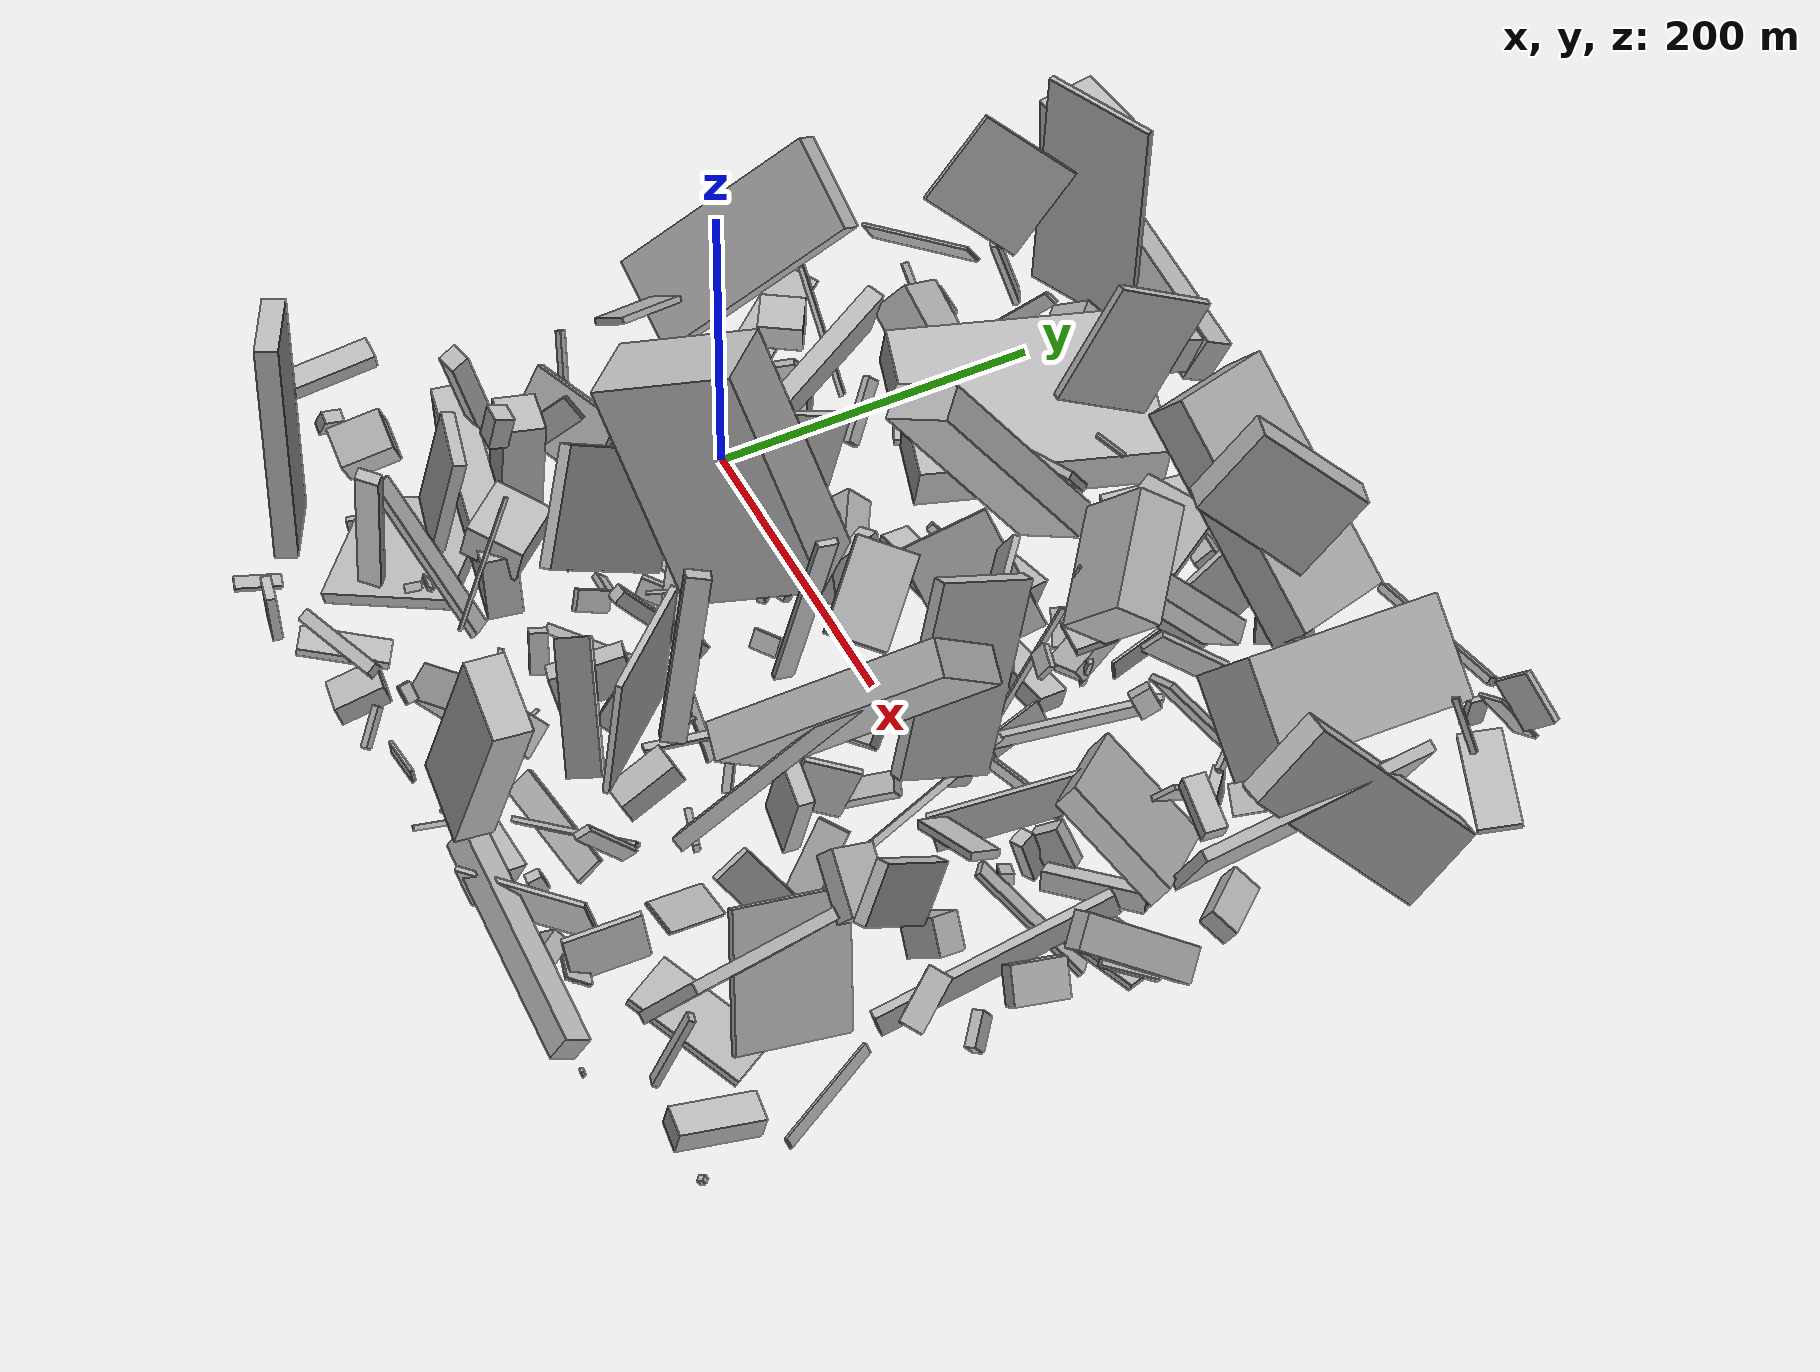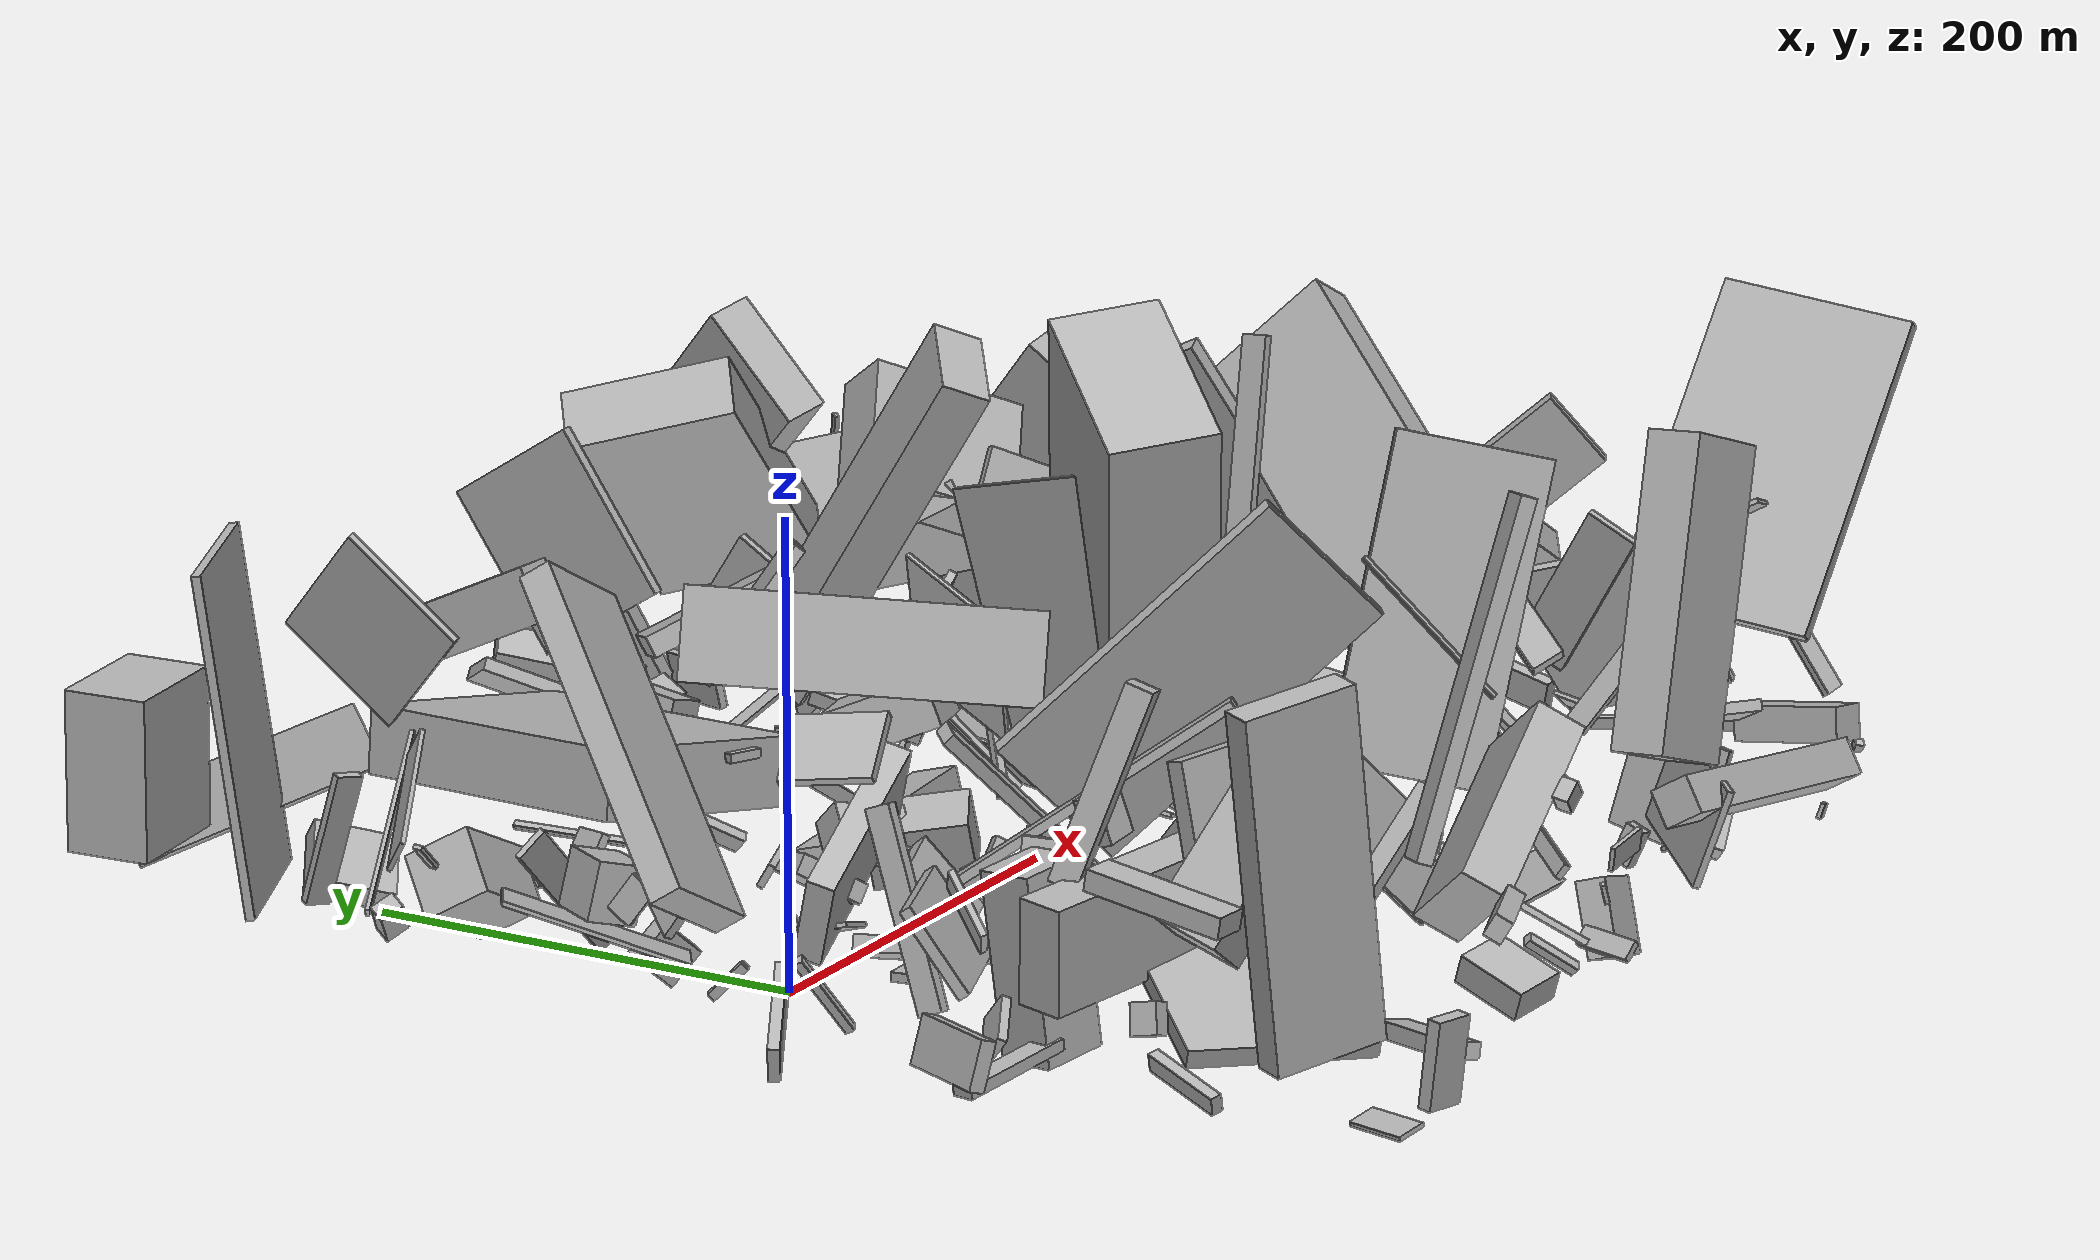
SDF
<sdf version="1.6">
 <world name="default">
  <scene>
   <sky><clouds><speed>12</speed></clouds></sky>
   <ambient>0.4 0.4 0.4 1</ambient>
   <background>0.7 0.7 0.7 1</background>
   <shadows>1</shadows>
  </scene>
  <gravity>0 0 -9.8066</gravity>
  <magnetic_field>6e-06 2.3e-05 -4.2e-05</magnetic_field>
  <physics default="0" name="default_physics" type="ode">
   <ode>
    <solver>
     <type>quick</type>
     <iters>10</iters>
     <sor>1.0</sor>
     <use_dynamic_moi_rescaling>0</use_dynamic_moi_rescaling>
    </solver>
    <constraints>
     <cfm>0</cfm>
     <erp>0.2</erp>
     <contact_max_correcting_vel>100</contact_max_correcting_vel>
     <contact_surface_layer>0.001</contact_surface_layer>
    </constraints>
   </ode>
   <max_step_size>0.004</max_step_size>
   <real_time_factor>1</real_time_factor>
   <real_time_update_rate>250</real_time_update_rate>
  </physics>
  <light name="sun" type="directional">
   <pose>0 0 10 0 0 0</pose>
   <diffuse>0.8 0.8 0.8 1</diffuse>
   <specular>0.2 0.2 0.2 1</specular>
   <attenuation>
    <range>1000</range>
    <constant>0.9</constant>
    <linear>0.01</linear>
    <quadratic>0.001</quadratic>
   </attenuation>
   <direction>-0.5 0.1 -0.9</direction>
  </light>
  <model name="building_1">
   <static>0</static>
   <pose>181.62778123430638 -56.829961058683004 104.75622870394925 0.41340760193390275 -0.12050947763218492 -0.797535893521868</pose>
   <link name="link">
    <gravity>0</gravity>
    <pose>0 0 75.0 0 0 0</pose>
    <collision name="collision"><geometry><box><size>47 89 150</size></box></geometry></collision>
    <visual name="visual">
     <cast_shadows>0</cast_shadows>
     <geometry><box><size>47 89 150</size></box></geometry>
     <material>
      <script>
       <uri>model://HANNAS_wall/materials/scripts</uri>
       <uri>model://HANNAS_wall/materials/textures</uri>
       <name>vrc/HANNAS_wall</name>
      </script>
     </material>
    </visual>
   </link>
  </model>
  <model name="building_2">
   <static>0</static>
   <pose>20.115930124817158 -164.19813199769504 38.87186801956815 0.05302751474850434 0.05117361558581353 -1.7988946004145192</pose>
   <link name="link">
    <gravity>0</gravity>
    <pose>0 0 22.5 0 0 0</pose>
    <collision name="collision"><geometry><box><size>21 150 45</size></box></geometry></collision>
    <visual name="visual">
     <cast_shadows>0</cast_shadows>
     <geometry><box><size>21 150 45</size></box></geometry>
     <material>
      <script>
       <uri>model://HANNAS_wall/materials/scripts</uri>
       <uri>model://HANNAS_wall/materials/textures</uri>
       <name>vrc/HANNAS_wall</name>
      </script>
     </material>
    </visual>
   </link>
  </model>
  <model name="building_3">
   <static>0</static>
   <pose>450.8930975170687 287.48173431054585 97.3096310186768 1.507844690463147 -0.8073381484602125 0.4057914663743679</pose>
   <link name="link">
    <gravity>0</gravity>
    <pose>0 0 2.0 0 0 0</pose>
    <collision name="collision"><geometry><box><size>30 33 4</size></box></geometry></collision>
    <visual name="visual">
     <cast_shadows>0</cast_shadows>
     <geometry><box><size>30 33 4</size></box></geometry>
     <material>
      <script>
       <uri>model://HANNAS_wall/materials/scripts</uri>
       <uri>model://HANNAS_wall/materials/textures</uri>
       <name>vrc/HANNAS_wall</name>
      </script>
     </material>
    </visual>
   </link>
  </model>
  <model name="building_4">
   <static>0</static>
   <pose>367.2085070339192 194.0304723521374 62.208197208277205 0.36969522379419045 -0.6738252039779774 3.1195512328538704</pose>
   <link name="link">
    <gravity>0</gravity>
    <pose>0 0 24.0 0 0 0</pose>
    <collision name="collision"><geometry><box><size>64 147 48</size></box></geometry></collision>
    <visual name="visual">
     <cast_shadows>0</cast_shadows>
     <geometry><box><size>64 147 48</size></box></geometry>
     <material>
      <script>
       <uri>model://HANNAS_wall/materials/scripts</uri>
       <uri>model://HANNAS_wall/materials/textures</uri>
       <name>vrc/HANNAS_wall</name>
      </script>
     </material>
    </visual>
   </link>
  </model>
  <model name="building_5">
   <static>0</static>
   <pose>366.93796762581417 -129.00037148774234 48.577309955742344 -2.7679729090759224 -0.8304152403304764 2.0013015284365134</pose>
   <link name="link">
    <gravity>0</gravity>
    <pose>0 0 2.0 0 0 0</pose>
    <collision name="collision"><geometry><box><size>98 19 4</size></box></geometry></collision>
    <visual name="visual">
     <cast_shadows>0</cast_shadows>
     <geometry><box><size>98 19 4</size></box></geometry>
     <material>
      <script>
       <uri>model://HANNAS_wall/materials/scripts</uri>
       <uri>model://HANNAS_wall/materials/textures</uri>
       <name>vrc/HANNAS_wall</name>
      </script>
     </material>
    </visual>
   </link>
  </model>
  <model name="building_6">
   <static>0</static>
   <pose>100.41339992611925 22.29559992179713 24.353771156262386 0.27460366340959924 0.7814450842973615 1.2354463447300463</pose>
   <link name="link">
    <gravity>0</gravity>
    <pose>0 0 11.0 0 0 0</pose>
    <collision name="collision"><geometry><box><size>18 33 22</size></box></geometry></collision>
    <visual name="visual">
     <cast_shadows>0</cast_shadows>
     <geometry><box><size>18 33 22</size></box></geometry>
     <material>
      <script>
       <uri>model://HANNAS_wall/materials/scripts</uri>
       <uri>model://HANNAS_wall/materials/textures</uri>
       <name>vrc/HANNAS_wall</name>
      </script>
     </material>
    </visual>
   </link>
  </model>
  <model name="building_7">
   <static>0</static>
   <pose>348.01590261600785 -30.969448456318037 88.29815140041796 -0.30418612962401714 0.4548619788155713 1.6481128041305757</pose>
   <link name="link">
    <gravity>0</gravity>
    <pose>0 0 59.0 0 0 0</pose>
    <collision name="collision"><geometry><box><size>64 9 118</size></box></geometry></collision>
    <visual name="visual">
     <cast_shadows>0</cast_shadows>
     <geometry><box><size>64 9 118</size></box></geometry>
     <material>
      <script>
       <uri>model://HANNAS_wall/materials/scripts</uri>
       <uri>model://HANNAS_wall/materials/textures</uri>
       <name>vrc/HANNAS_wall</name>
      </script>
     </material>
    </visual>
   </link>
  </model>
  <model name="building_8">
   <static>0</static>
   <pose>358.8000319206011 53.29572700275003 62.51961602610329 2.33568567704145 -0.6957634132902295 1.4990765797685028</pose>
   <link name="link">
    <gravity>0</gravity>
    <pose>0 0 39.0 0 0 0</pose>
    <collision name="collision"><geometry><box><size>15 128 78</size></box></geometry></collision>
    <visual name="visual">
     <cast_shadows>0</cast_shadows>
     <geometry><box><size>15 128 78</size></box></geometry>
     <material>
      <script>
       <uri>model://HANNAS_wall/materials/scripts</uri>
       <uri>model://HANNAS_wall/materials/textures</uri>
       <name>vrc/HANNAS_wall</name>
      </script>
     </material>
    </visual>
   </link>
  </model>
  <model name="building_9">
   <static>0</static>
   <pose>202.92018784832817 114.92015161486549 89.3930528797136 0.41424176409778923 -0.410473397821822 0.6333548334155709</pose>
   <link name="link">
    <gravity>0</gravity>
    <pose>0 0 75.0 0 0 0</pose>
    <collision name="collision"><geometry><box><size>42 22 150</size></box></geometry></collision>
    <visual name="visual">
     <cast_shadows>0</cast_shadows>
     <geometry><box><size>42 22 150</size></box></geometry>
     <material>
      <script>
       <uri>model://HANNAS_wall/materials/scripts</uri>
       <uri>model://HANNAS_wall/materials/textures</uri>
       <name>vrc/HANNAS_wall</name>
      </script>
     </material>
    </visual>
   </link>
  </model>
  <model name="building_10">
   <static>0</static>
   <pose>-14.653882508272398 -234.8858611273966 21.38120555154649 -0.1643764812842645 -1.313797045708349 -2.1714278078921576</pose>
   <link name="link">
    <gravity>0</gravity>
    <pose>0 0 40.5 0 0 0</pose>
    <collision name="collision"><geometry><box><size>8 79 81</size></box></geometry></collision>
    <visual name="visual">
     <cast_shadows>0</cast_shadows>
     <geometry><box><size>8 79 81</size></box></geometry>
     <material>
      <script>
       <uri>model://HANNAS_wall/materials/scripts</uri>
       <uri>model://HANNAS_wall/materials/textures</uri>
       <name>vrc/HANNAS_wall</name>
      </script>
     </material>
    </visual>
   </link>
  </model>
  <model name="building_11">
   <static>0</static>
   <pose>81.60038833937313 155.5969478903069 38.42744125661743 0.0870294544799585 -0.15905743890190527 2.8782792268598842</pose>
   <link name="link">
    <gravity>0</gravity>
    <pose>0 0 15.0 0 0 0</pose>
    <collision name="collision"><geometry><box><size>104 150 30</size></box></geometry></collision>
    <visual name="visual">
     <cast_shadows>0</cast_shadows>
     <geometry><box><size>104 150 30</size></box></geometry>
     <material>
      <script>
       <uri>model://HANNAS_wall/materials/scripts</uri>
       <uri>model://HANNAS_wall/materials/textures</uri>
       <name>vrc/HANNAS_wall</name>
      </script>
     </material>
    </visual>
   </link>
  </model>
  <model name="building_12">
   <static>0</static>
   <pose>200.65052059249666 68.99652779053706 43.300755149841706 0.3837364830169382 -0.14467282643756932 -2.782687314562869</pose>
   <link name="link">
    <gravity>0</gravity>
    <pose>0 0 11.0 0 0 0</pose>
    <collision name="collision"><geometry><box><size>46 48 22</size></box></geometry></collision>
    <visual name="visual">
     <cast_shadows>0</cast_shadows>
     <geometry><box><size>46 48 22</size></box></geometry>
     <material>
      <script>
       <uri>model://HANNAS_wall/materials/scripts</uri>
       <uri>model://HANNAS_wall/materials/textures</uri>
       <name>vrc/HANNAS_wall</name>
      </script>
     </material>
    </visual>
   </link>
  </model>
  <model name="building_13">
   <static>0</static>
   <pose>303.5498627580629 -202.1273397119324 62.30362091075866 0.4281541827251762 -0.4826214191146808 1.4194697516153478</pose>
   <link name="link">
    <gravity>0</gravity>
    <pose>0 0 42.5 0 0 0</pose>
    <collision name="collision"><geometry><box><size>10 4 85</size></box></geometry></collision>
    <visual name="visual">
     <cast_shadows>0</cast_shadows>
     <geometry><box><size>10 4 85</size></box></geometry>
     <material>
      <script>
       <uri>model://HANNAS_wall/materials/scripts</uri>
       <uri>model://HANNAS_wall/materials/textures</uri>
       <name>vrc/HANNAS_wall</name>
      </script>
     </material>
    </visual>
   </link>
  </model>
  <model name="building_14">
   <static>0</static>
   <pose>338.52106458638247 -30.991828954077725 29.410397892295503 -1.338100842568727 -0.15729105979023997 -0.32407212823067116</pose>
   <link name="link">
    <gravity>0</gravity>
    <pose>0 0 46.5 0 0 0</pose>
    <collision name="collision"><geometry><box><size>4 26 93</size></box></geometry></collision>
    <visual name="visual">
     <cast_shadows>0</cast_shadows>
     <geometry><box><size>4 26 93</size></box></geometry>
     <material>
      <script>
       <uri>model://HANNAS_wall/materials/scripts</uri>
       <uri>model://HANNAS_wall/materials/textures</uri>
       <name>vrc/HANNAS_wall</name>
      </script>
     </material>
    </visual>
   </link>
  </model>
  <model name="building_15">
   <static>0</static>
   <pose>150.29541065074352 -5.62952348746983 116.93909951079544 1.3074179471680738 -0.06561653426909896 -0.2005784589073619</pose>
   <link name="link">
    <gravity>0</gravity>
    <pose>0 0 38.5 0 0 0</pose>
    <collision name="collision"><geometry><box><size>4 120 77</size></box></geometry></collision>
    <visual name="visual">
     <cast_shadows>0</cast_shadows>
     <geometry><box><size>4 120 77</size></box></geometry>
     <material>
      <script>
       <uri>model://HANNAS_wall/materials/scripts</uri>
       <uri>model://HANNAS_wall/materials/textures</uri>
       <name>vrc/HANNAS_wall</name>
      </script>
     </material>
    </visual>
   </link>
  </model>
  <model name="building_16">
   <static>0</static>
   <pose>253.31720954136728 2.3002131281182394 39.780277177644976 -0.01482352069662092 -0.9229812678496938 0.27385160361569905</pose>
   <link name="link">
    <gravity>0</gravity>
    <pose>0 0 2.0 0 0 0</pose>
    <collision name="collision"><geometry><box><size>47 37 4</size></box></geometry></collision>
    <visual name="visual">
     <cast_shadows>0</cast_shadows>
     <geometry><box><size>47 37 4</size></box></geometry>
     <material>
      <script>
       <uri>model://HANNAS_wall/materials/scripts</uri>
       <uri>model://HANNAS_wall/materials/textures</uri>
       <name>vrc/HANNAS_wall</name>
      </script>
     </material>
    </visual>
   </link>
  </model>
  <model name="building_17">
   <static>0</static>
   <pose>55.57145236262984 -222.6436472532139 50.40587718873466 -0.7411034410752321 0.10081316057884478 -1.845032765059312</pose>
   <link name="link">
    <gravity>0</gravity>
    <pose>0 0 33.5 0 0 0</pose>
    <collision name="collision"><geometry><box><size>10 5 67</size></box></geometry></collision>
    <visual name="visual">
     <cast_shadows>0</cast_shadows>
     <geometry><box><size>10 5 67</size></box></geometry>
     <material>
      <script>
       <uri>model://HANNAS_wall/materials/scripts</uri>
       <uri>model://HANNAS_wall/materials/textures</uri>
       <name>vrc/HANNAS_wall</name>
      </script>
     </material>
    </visual>
   </link>
  </model>
  <model name="building_18">
   <static>0</static>
   <pose>255.98294651979657 -143.66773095367154 20.143360686291402 -1.0476216306297381 0.12492093657156894 -1.8495851556932774</pose>
   <link name="link">
    <gravity>0</gravity>
    <pose>0 0 32.5 0 0 0</pose>
    <collision name="collision"><geometry><box><size>4 4 65</size></box></geometry></collision>
    <visual name="visual">
     <cast_shadows>0</cast_shadows>
     <geometry><box><size>4 4 65</size></box></geometry>
     <material>
      <script>
       <uri>model://HANNAS_wall/materials/scripts</uri>
       <uri>model://HANNAS_wall/materials/textures</uri>
       <name>vrc/HANNAS_wall</name>
      </script>
     </material>
    </visual>
   </link>
  </model>
  <model name="building_19">
   <static>0</static>
   <pose>233.4228596078339 -72.72268597515381 78.13247146226202 -0.2635942836586963 -0.09601195973758359 -1.693818515565837</pose>
   <link name="link">
    <gravity>0</gravity>
    <pose>0 0 75.0 0 0 0</pose>
    <collision name="collision"><geometry><box><size>12 4 150</size></box></geometry></collision>
    <visual name="visual">
     <cast_shadows>0</cast_shadows>
     <geometry><box><size>12 4 150</size></box></geometry>
     <material>
      <script>
       <uri>model://HANNAS_wall/materials/scripts</uri>
       <uri>model://HANNAS_wall/materials/textures</uri>
       <name>vrc/HANNAS_wall</name>
      </script>
     </material>
    </visual>
   </link>
  </model>
  <model name="building_20">
   <static>0</static>
   <pose>393.7164438287608 -140.93135978355008 61.7795820910733 0.16048409968176683 0.5082068844359077 -1.4412710564936078</pose>
   <link name="link">
    <gravity>0</gravity>
    <pose>0 0 37.5 0 0 0</pose>
    <collision name="collision"><geometry><box><size>24 4 75</size></box></geometry></collision>
    <visual name="visual">
     <cast_shadows>0</cast_shadows>
     <geometry><box><size>24 4 75</size></box></geometry>
     <material>
      <script>
       <uri>model://HANNAS_wall/materials/scripts</uri>
       <uri>model://HANNAS_wall/materials/textures</uri>
       <name>vrc/HANNAS_wall</name>
      </script>
     </material>
    </visual>
   </link>
  </model>
  <model name="building_21">
   <static>0</static>
   <pose>230.0842074939692 -208.09408159664707 22.94398390310819 -2.2755186249988264 -0.14356960257799212 -2.9904671393988087</pose>
   <link name="link">
    <gravity>0</gravity>
    <pose>0 0 9.0 0 0 0</pose>
    <collision name="collision"><geometry><box><size>73 4 18</size></box></geometry></collision>
    <visual name="visual">
     <cast_shadows>0</cast_shadows>
     <geometry><box><size>73 4 18</size></box></geometry>
     <material>
      <script>
       <uri>model://HANNAS_wall/materials/scripts</uri>
       <uri>model://HANNAS_wall/materials/textures</uri>
       <name>vrc/HANNAS_wall</name>
      </script>
     </material>
    </visual>
   </link>
  </model>
  <model name="building_22">
   <static>0</static>
   <pose>237.8671128048006 -275.3264804529206 78.6715799147138 0.3375347821358153 0.08022363856202351 1.5163037522461518</pose>
   <link name="link">
    <gravity>0</gravity>
    <pose>0 0 66.5 0 0 0</pose>
    <collision name="collision"><geometry><box><size>24 49 133</size></box></geometry></collision>
    <visual name="visual">
     <cast_shadows>0</cast_shadows>
     <geometry><box><size>24 49 133</size></box></geometry>
     <material>
      <script>
       <uri>model://HANNAS_wall/materials/scripts</uri>
       <uri>model://HANNAS_wall/materials/textures</uri>
       <name>vrc/HANNAS_wall</name>
      </script>
     </material>
    </visual>
   </link>
  </model>
  <model name="building_23">
   <static>0</static>
   <pose>-9.901311223835938 56.50516448297498 44.13695730878735 -2.01343031328651 -0.39806591463981833 2.6599263963321573</pose>
   <link name="link">
    <gravity>0</gravity>
    <pose>0 0 14.5 0 0 0</pose>
    <collision name="collision"><geometry><box><size>4 19 29</size></box></geometry></collision>
    <visual name="visual">
     <cast_shadows>0</cast_shadows>
     <geometry><box><size>4 19 29</size></box></geometry>
     <material>
      <script>
       <uri>model://HANNAS_wall/materials/scripts</uri>
       <uri>model://HANNAS_wall/materials/textures</uri>
       <name>vrc/HANNAS_wall</name>
      </script>
     </material>
    </visual>
   </link>
  </model>
  <model name="building_24">
   <static>0</static>
   <pose>200.56718997824925 198.07591988099784 63.95120900199447 0.5704566773049597 -1.0674264048297555 1.729349936935957</pose>
   <link name="link">
    <gravity>0</gravity>
    <pose>0 0 75.0 0 0 0</pose>
    <collision name="collision"><geometry><box><size>10 47 150</size></box></geometry></collision>
    <visual name="visual">
     <cast_shadows>0</cast_shadows>
     <geometry><box><size>10 47 150</size></box></geometry>
     <material>
      <script>
       <uri>model://HANNAS_wall/materials/scripts</uri>
       <uri>model://HANNAS_wall/materials/textures</uri>
       <name>vrc/HANNAS_wall</name>
      </script>
     </material>
    </visual>
   </link>
  </model>
  <model name="building_25">
   <static>0</static>
   <pose>82.06618334382708 -109.70899137280261 12.911439734087468 -1.81425020537896 0.7407651662791405 1.3296588367044313</pose>
   <link name="link">
    <gravity>0</gravity>
    <pose>0 0 11.0 0 0 0</pose>
    <collision name="collision"><geometry><box><size>8 4 22</size></box></geometry></collision>
    <visual name="visual">
     <cast_shadows>0</cast_shadows>
     <geometry><box><size>8 4 22</size></box></geometry>
     <material>
      <script>
       <uri>model://HANNAS_wall/materials/scripts</uri>
       <uri>model://HANNAS_wall/materials/textures</uri>
       <name>vrc/HANNAS_wall</name>
      </script>
     </material>
    </visual>
   </link>
  </model>
  <model name="building_26">
   <static>0</static>
   <pose>207.22941711827144 266.40305713704504 29.6174458225779 0.7192496795375679 -0.9073419525765692 0.1526931062896808</pose>
   <link name="link">
    <gravity>0</gravity>
    <pose>0 0 11.0 0 0 0</pose>
    <collision name="collision"><geometry><box><size>6 55 22</size></box></geometry></collision>
    <visual name="visual">
     <cast_shadows>0</cast_shadows>
     <geometry><box><size>6 55 22</size></box></geometry>
     <material>
      <script>
       <uri>model://HANNAS_wall/materials/scripts</uri>
       <uri>model://HANNAS_wall/materials/textures</uri>
       <name>vrc/HANNAS_wall</name>
      </script>
     </material>
    </visual>
   </link>
  </model>
  <model name="building_27">
   <static>0</static>
   <pose>423.2838466854882 -208.67709415920035 81.82649826413133 0.1413094886405997 0.6122159057931443 0.15823957279419285</pose>
   <link name="link">
    <gravity>0</gravity>
    <pose>0 0 75.0 0 0 0</pose>
    <collision name="collision"><geometry><box><size>7 88 150</size></box></geometry></collision>
    <visual name="visual">
     <cast_shadows>0</cast_shadows>
     <geometry><box><size>7 88 150</size></box></geometry>
     <material>
      <script>
       <uri>model://HANNAS_wall/materials/scripts</uri>
       <uri>model://HANNAS_wall/materials/textures</uri>
       <name>vrc/HANNAS_wall</name>
      </script>
     </material>
    </visual>
   </link>
  </model>
  <model name="building_28">
   <static>0</static>
   <pose>328.0388374397415 139.2967949768567 34.741643637846025 -0.6937214261656218 -0.8466862311553371 -2.2370734669124728</pose>
   <link name="link">
    <gravity>0</gravity>
    <pose>0 0 13.0 0 0 0</pose>
    <collision name="collision"><geometry><box><size>72 4 26</size></box></geometry></collision>
    <visual name="visual">
     <cast_shadows>0</cast_shadows>
     <geometry><box><size>72 4 26</size></box></geometry>
     <material>
      <script>
       <uri>model://HANNAS_wall/materials/scripts</uri>
       <uri>model://HANNAS_wall/materials/textures</uri>
       <name>vrc/HANNAS_wall</name>
      </script>
     </material>
    </visual>
   </link>
  </model>
  <model name="building_29">
   <static>0</static>
   <pose>64.6198443517878 -97.30763751534842 78.0623768036405 1.761979795424307 -0.9644688415030647 1.870822670234923</pose>
   <link name="link">
    <gravity>0</gravity>
    <pose>0 0 5.0 0 0 0</pose>
    <collision name="collision"><geometry><box><size>4 150 10</size></box></geometry></collision>
    <visual name="visual">
     <cast_shadows>0</cast_shadows>
     <geometry><box><size>4 150 10</size></box></geometry>
     <material>
      <script>
       <uri>model://HANNAS_wall/materials/scripts</uri>
       <uri>model://HANNAS_wall/materials/textures</uri>
       <name>vrc/HANNAS_wall</name>
      </script>
     </material>
    </visual>
   </link>
  </model>
  <model name="building_30">
   <static>0</static>
   <pose>433.81226036326905 -79.0754404706614 102.59673930444904 -0.09920087051929398 -0.8556372474861931 2.1366737547197134</pose>
   <link name="link">
    <gravity>0</gravity>
    <pose>0 0 34.5 0 0 0</pose>
    <collision name="collision"><geometry><box><size>38 8 69</size></box></geometry></collision>
    <visual name="visual">
     <cast_shadows>0</cast_shadows>
     <geometry><box><size>38 8 69</size></box></geometry>
     <material>
      <script>
       <uri>model://HANNAS_wall/materials/scripts</uri>
       <uri>model://HANNAS_wall/materials/textures</uri>
       <name>vrc/HANNAS_wall</name>
      </script>
     </material>
    </visual>
   </link>
  </model>
  <model name="building_31">
   <static>0</static>
   <pose>323.8296388341633 -179.14422340837856 81.77296150881438 -0.615209230431995 0.5990761632010638 0.41969506388018735</pose>
   <link name="link">
    <gravity>0</gravity>
    <pose>0 0 71.0 0 0 0</pose>
    <collision name="collision"><geometry><box><size>9 15 142</size></box></geometry></collision>
    <visual name="visual">
     <cast_shadows>0</cast_shadows>
     <geometry><box><size>9 15 142</size></box></geometry>
     <material>
      <script>
       <uri>model://HANNAS_wall/materials/scripts</uri>
       <uri>model://HANNAS_wall/materials/textures</uri>
       <name>vrc/HANNAS_wall</name>
      </script>
     </material>
    </visual>
   </link>
  </model>
  <model name="building_32">
   <static>0</static>
   <pose>283.65210716667843 -90.75363850722815 48.33629093482091 -3.0502330619504185 1.1958537590814935 -1.8912091224020218</pose>
   <link name="link">
    <gravity>0</gravity>
    <pose>0 0 17.5 0 0 0</pose>
    <collision name="collision"><geometry><box><size>37 4 35</size></box></geometry></collision>
    <visual name="visual">
     <cast_shadows>0</cast_shadows>
     <geometry><box><size>37 4 35</size></box></geometry>
     <material>
      <script>
       <uri>model://HANNAS_wall/materials/scripts</uri>
       <uri>model://HANNAS_wall/materials/textures</uri>
       <name>vrc/HANNAS_wall</name>
      </script>
     </material>
    </visual>
   </link>
  </model>
  <model name="building_33">
   <static>0</static>
   <pose>112.37411288349234 -170.54389705355626 28.919201019426623 -1.1468998049021748 -0.021981084122898717 -1.9338927442164555</pose>
   <link name="link">
    <gravity>0</gravity>
    <pose>0 0 4.0 0 0 0</pose>
    <collision name="collision"><geometry><box><size>11 26 8</size></box></geometry></collision>
    <visual name="visual">
     <cast_shadows>0</cast_shadows>
     <geometry><box><size>11 26 8</size></box></geometry>
     <material>
      <script>
       <uri>model://HANNAS_wall/materials/scripts</uri>
       <uri>model://HANNAS_wall/materials/textures</uri>
       <name>vrc/HANNAS_wall</name>
      </script>
     </material>
    </visual>
   </link>
  </model>
  <model name="building_34">
   <static>0</static>
   <pose>300.5026610406594 -131.03983425655088 114.70064448822038 -0.7383841029522928 -0.7566949573000991 -1.1854946712340908</pose>
   <link name="link">
    <gravity>0</gravity>
    <pose>0 0 75.0 0 0 0</pose>
    <collision name="collision"><geometry><box><size>67 23 150</size></box></geometry></collision>
    <visual name="visual">
     <cast_shadows>0</cast_shadows>
     <geometry><box><size>67 23 150</size></box></geometry>
     <material>
      <script>
       <uri>model://HANNAS_wall/materials/scripts</uri>
       <uri>model://HANNAS_wall/materials/textures</uri>
       <name>vrc/HANNAS_wall</name>
      </script>
     </material>
    </visual>
   </link>
  </model>
  <model name="building_35">
   <static>0</static>
   <pose>87.37654608307663 275.29059221368243 38.88797717263988 1.5463377264508071 -0.5480142295324905 -1.5693445576273866</pose>
   <link name="link">
    <gravity>0</gravity>
    <pose>0 0 75.0 0 0 0</pose>
    <collision name="collision"><geometry><box><size>19 29 150</size></box></geometry></collision>
    <visual name="visual">
     <cast_shadows>0</cast_shadows>
     <geometry><box><size>19 29 150</size></box></geometry>
     <material>
      <script>
       <uri>model://HANNAS_wall/materials/scripts</uri>
       <uri>model://HANNAS_wall/materials/textures</uri>
       <name>vrc/HANNAS_wall</name>
      </script>
     </material>
    </visual>
   </link>
  </model>
  <model name="building_36">
   <static>0</static>
   <pose>277.0481197221919 -16.38829590633877 21.1454384522796 -1.436703308358964 -1.0622199861069026 -0.3310575167198313</pose>
   <link name="link">
    <gravity>0</gravity>
    <pose>0 0 75.0 0 0 0</pose>
    <collision name="collision"><geometry><box><size>28 4 150</size></box></geometry></collision>
    <visual name="visual">
     <cast_shadows>0</cast_shadows>
     <geometry><box><size>28 4 150</size></box></geometry>
     <material>
      <script>
       <uri>model://HANNAS_wall/materials/scripts</uri>
       <uri>model://HANNAS_wall/materials/textures</uri>
       <name>vrc/HANNAS_wall</name>
      </script>
     </material>
    </visual>
   </link>
  </model>
  <model name="building_37">
   <static>0</static>
   <pose>-64.60249120097326 276.45399733383454 38.38960875734548 -0.021199643157860746 0.007752772517476573 -3.014206578636452</pose>
   <link name="link">
    <gravity>0</gravity>
    <pose>0 0 35.0 0 0 0</pose>
    <collision name="collision"><geometry><box><size>54 37 70</size></box></geometry></collision>
    <visual name="visual">
     <cast_shadows>0</cast_shadows>
     <geometry><box><size>54 37 70</size></box></geometry>
     <material>
      <script>
       <uri>model://HANNAS_wall/materials/scripts</uri>
       <uri>model://HANNAS_wall/materials/textures</uri>
       <name>vrc/HANNAS_wall</name>
      </script>
     </material>
    </visual>
   </link>
  </model>
  <model name="building_38">
   <static>0</static>
   <pose>464.1576836696233 96.77750329843218 36.46694940271851 -2.514524869911133 0.19679357910353318 2.3549243766485066</pose>
   <link name="link">
    <gravity>0</gravity>
    <pose>0 0 6.0 0 0 0</pose>
    <collision name="collision"><geometry><box><size>44 19 12</size></box></geometry></collision>
    <visual name="visual">
     <cast_shadows>0</cast_shadows>
     <geometry><box><size>44 19 12</size></box></geometry>
     <material>
      <script>
       <uri>model://HANNAS_wall/materials/scripts</uri>
       <uri>model://HANNAS_wall/materials/textures</uri>
       <name>vrc/HANNAS_wall</name>
      </script>
     </material>
    </visual>
   </link>
  </model>
  <model name="building_39">
   <static>0</static>
   <pose>261.3214544324071 209.63113531645956 111.17041259311725 0.32634068536976996 -0.7096972280868387 -2.9269833830023058</pose>
   <link name="link">
    <gravity>0</gravity>
    <pose>0 0 14.0 0 0 0</pose>
    <collision name="collision"><geometry><box><size>150 76 28</size></box></geometry></collision>
    <visual name="visual">
     <cast_shadows>0</cast_shadows>
     <geometry><box><size>150 76 28</size></box></geometry>
     <material>
      <script>
       <uri>model://HANNAS_wall/materials/scripts</uri>
       <uri>model://HANNAS_wall/materials/textures</uri>
       <name>vrc/HANNAS_wall</name>
      </script>
     </material>
    </visual>
   </link>
  </model>
  <model name="building_40">
   <static>0</static>
   <pose>276.9879266689189 100.03314976470202 71.57198929916207 -0.14353702798734272 0.2353346117044769 2.974491918062972</pose>
   <link name="link">
    <gravity>0</gravity>
    <pose>0 0 2.0 0 0 0</pose>
    <collision name="collision"><geometry><box><size>31 25 4</size></box></geometry></collision>
    <visual name="visual">
     <cast_shadows>0</cast_shadows>
     <geometry><box><size>31 25 4</size></box></geometry>
     <material>
      <script>
       <uri>model://HANNAS_wall/materials/scripts</uri>
       <uri>model://HANNAS_wall/materials/textures</uri>
       <name>vrc/HANNAS_wall</name>
      </script>
     </material>
    </visual>
   </link>
  </model>
  <model name="building_41">
   <static>0</static>
   <pose>-3.1355635308226386 -62.61574151499572 48.77479102769235 -2.6857091984338752 -1.1535623427216741 1.1895858620108335</pose>
   <link name="link">
    <gravity>0</gravity>
    <pose>0 0 5.5 0 0 0</pose>
    <collision name="collision"><geometry><box><size>86 6 11</size></box></geometry></collision>
    <visual name="visual">
     <cast_shadows>0</cast_shadows>
     <geometry><box><size>86 6 11</size></box></geometry>
     <material>
      <script>
       <uri>model://HANNAS_wall/materials/scripts</uri>
       <uri>model://HANNAS_wall/materials/textures</uri>
       <name>vrc/HANNAS_wall</name>
      </script>
     </material>
    </visual>
   </link>
  </model>
  <model name="building_42">
   <static>0</static>
   <pose>-40.27949720575122 -42.5652916731845 108.23680996056456 -0.8986041245170789 -0.1431406556665133 -1.4053886569828866</pose>
   <link name="link">
    <gravity>0</gravity>
    <pose>0 0 16.0 0 0 0</pose>
    <collision name="collision"><geometry><box><size>41 4 32</size></box></geometry></collision>
    <visual name="visual">
     <cast_shadows>0</cast_shadows>
     <geometry><box><size>41 4 32</size></box></geometry>
     <material>
      <script>
       <uri>model://HANNAS_wall/materials/scripts</uri>
       <uri>model://HANNAS_wall/materials/textures</uri>
       <name>vrc/HANNAS_wall</name>
      </script>
     </material>
    </visual>
   </link>
  </model>
  <model name="building_43">
   <static>0</static>
   <pose>422.1462973297976 -123.29589621330148 56.18898946469028 -0.9815457062298355 -0.9810275654083641 2.7188622036323804</pose>
   <link name="link">
    <gravity>0</gravity>
    <pose>0 0 39.5 0 0 0</pose>
    <collision name="collision"><geometry><box><size>84 4 79</size></box></geometry></collision>
    <visual name="visual">
     <cast_shadows>0</cast_shadows>
     <geometry><box><size>84 4 79</size></box></geometry>
     <material>
      <script>
       <uri>model://HANNAS_wall/materials/scripts</uri>
       <uri>model://HANNAS_wall/materials/textures</uri>
       <name>vrc/HANNAS_wall</name>
      </script>
     </material>
    </visual>
   </link>
  </model>
  <model name="building_44">
   <static>0</static>
   <pose>428.2304037989306 -14.65644072804095 34.449330334265674 1.7291601171601512 0.7612280484340336 -2.1265610803290453</pose>
   <link name="link">
    <gravity>0</gravity>
    <pose>0 0 5.5 0 0 0</pose>
    <collision name="collision"><geometry><box><size>4 88 11</size></box></geometry></collision>
    <visual name="visual">
     <cast_shadows>0</cast_shadows>
     <geometry><box><size>4 88 11</size></box></geometry>
     <material>
      <script>
       <uri>model://HANNAS_wall/materials/scripts</uri>
       <uri>model://HANNAS_wall/materials/textures</uri>
       <name>vrc/HANNAS_wall</name>
      </script>
     </material>
    </visual>
   </link>
  </model>
  <model name="building_45">
   <static>0</static>
   <pose>-21.53232263623066 -100.40113677014267 31.678432481188562 0.07042741839347301 0.6018804615805614 1.9922401877541265</pose>
   <link name="link">
    <gravity>0</gravity>
    <pose>0 0 21.0 0 0 0</pose>
    <collision name="collision"><geometry><box><size>5 63 42</size></box></geometry></collision>
    <visual name="visual">
     <cast_shadows>0</cast_shadows>
     <geometry><box><size>5 63 42</size></box></geometry>
     <material>
      <script>
       <uri>model://HANNAS_wall/materials/scripts</uri>
       <uri>model://HANNAS_wall/materials/textures</uri>
       <name>vrc/HANNAS_wall</name>
      </script>
     </material>
    </visual>
   </link>
  </model>
  <model name="building_46">
   <static>0</static>
   <pose>-13.046258868459958 149.61007165047752 39.28430234622244 2.620481557693868 -0.4990777187596904 -1.2202207706091</pose>
   <link name="link">
    <gravity>0</gravity>
    <pose>0 0 14.5 0 0 0</pose>
    <collision name="collision"><geometry><box><size>30 51 29</size></box></geometry></collision>
    <visual name="visual">
     <cast_shadows>0</cast_shadows>
     <geometry><box><size>30 51 29</size></box></geometry>
     <material>
      <script>
       <uri>model://HANNAS_wall/materials/scripts</uri>
       <uri>model://HANNAS_wall/materials/textures</uri>
       <name>vrc/HANNAS_wall</name>
      </script>
     </material>
    </visual>
   </link>
  </model>
  <model name="building_47">
   <static>0</static>
   <pose>408.88793407285306 36.912778225462894 12.166605865511102 0.40511841900523166 0.03553645866096697 -2.351190383416803</pose>
   <link name="link">
    <gravity>0</gravity>
    <pose>0 0 6.0 0 0 0</pose>
    <collision name="collision"><geometry><box><size>62 14 12</size></box></geometry></collision>
    <visual name="visual">
     <cast_shadows>0</cast_shadows>
     <geometry><box><size>62 14 12</size></box></geometry>
     <material>
      <script>
       <uri>model://HANNAS_wall/materials/scripts</uri>
       <uri>model://HANNAS_wall/materials/textures</uri>
       <name>vrc/HANNAS_wall</name>
      </script>
     </material>
    </visual>
   </link>
  </model>
  <model name="building_48">
   <static>0</static>
   <pose>59.304486040489145 -154.61539108928577 89.2467785555956 1.615810645872121 0.22770645034867296 0.690434921098013</pose>
   <link name="link">
    <gravity>0</gravity>
    <pose>0 0 19.5 0 0 0</pose>
    <collision name="collision"><geometry><box><size>36 25 39</size></box></geometry></collision>
    <visual name="visual">
     <cast_shadows>0</cast_shadows>
     <geometry><box><size>36 25 39</size></box></geometry>
     <material>
      <script>
       <uri>model://HANNAS_wall/materials/scripts</uri>
       <uri>model://HANNAS_wall/materials/textures</uri>
       <name>vrc/HANNAS_wall</name>
      </script>
     </material>
    </visual>
   </link>
  </model>
  <model name="building_49">
   <static>0</static>
   <pose>475.37248958033126 172.39972605572916 77.97186868393027 1.8031140768209986 -0.8954587846537511 -1.7441668914271056</pose>
   <link name="link">
    <gravity>0</gravity>
    <pose>0 0 9.0 0 0 0</pose>
    <collision name="collision"><geometry><box><size>150 55 18</size></box></geometry></collision>
    <visual name="visual">
     <cast_shadows>0</cast_shadows>
     <geometry><box><size>150 55 18</size></box></geometry>
     <material>
      <script>
       <uri>model://HANNAS_wall/materials/scripts</uri>
       <uri>model://HANNAS_wall/materials/textures</uri>
       <name>vrc/HANNAS_wall</name>
      </script>
     </material>
    </visual>
   </link>
  </model>
  <model name="building_50">
   <static>0</static>
   <pose>396.22445277598064 -281.97709241901384 33.79744834901935 -1.3875249333521755 0.5524911589988926 1.6293658633441293</pose>
   <link name="link">
    <gravity>0</gravity>
    <pose>0 0 75.0 0 0 0</pose>
    <collision name="collision"><geometry><box><size>18 17 150</size></box></geometry></collision>
    <visual name="visual">
     <cast_shadows>0</cast_shadows>
     <geometry><box><size>18 17 150</size></box></geometry>
     <material>
      <script>
       <uri>model://HANNAS_wall/materials/scripts</uri>
       <uri>model://HANNAS_wall/materials/textures</uri>
       <name>vrc/HANNAS_wall</name>
      </script>
     </material>
    </visual>
   </link>
  </model>
  <model name="building_51">
   <static>0</static>
   <pose>-1.845372617270687 51.56690049891347 16.8805968858292 2.9980482731381564 -0.7351074389704401 2.668659597247639</pose>
   <link name="link">
    <gravity>0</gravity>
    <pose>0 0 9.5 0 0 0</pose>
    <collision name="collision"><geometry><box><size>22 9 19</size></box></geometry></collision>
    <visual name="visual">
     <cast_shadows>0</cast_shadows>
     <geometry><box><size>22 9 19</size></box></geometry>
     <material>
      <script>
       <uri>model://HANNAS_wall/materials/scripts</uri>
       <uri>model://HANNAS_wall/materials/textures</uri>
       <name>vrc/HANNAS_wall</name>
      </script>
     </material>
    </visual>
   </link>
  </model>
  <model name="building_52">
   <static>0</static>
   <pose>72.72170848542366 146.3348516806358 14.270329781232471 0.5732673839932478 0.10949052292096213 1.16327463975699</pose>
   <link name="link">
    <gravity>0</gravity>
    <pose>0 0 5.0 0 0 0</pose>
    <collision name="collision"><geometry><box><size>18 4 10</size></box></geometry></collision>
    <visual name="visual">
     <cast_shadows>0</cast_shadows>
     <geometry><box><size>18 4 10</size></box></geometry>
     <material>
      <script>
       <uri>model://HANNAS_wall/materials/scripts</uri>
       <uri>model://HANNAS_wall/materials/textures</uri>
       <name>vrc/HANNAS_wall</name>
      </script>
     </material>
    </visual>
   </link>
  </model>
  <model name="building_53">
   <static>0</static>
   <pose>258.8851005368619 255.14816545746297 5.8913647735968375 -0.0833760310381549 -0.1833674534385705 -2.574256198408164</pose>
   <link name="link">
    <gravity>0</gravity>
    <pose>0 0 2.0 0 0 0</pose>
    <collision name="collision"><geometry><box><size>4 35 4</size></box></geometry></collision>
    <visual name="visual">
     <cast_shadows>0</cast_shadows>
     <geometry><box><size>4 35 4</size></box></geometry>
     <material>
      <script>
       <uri>model://HANNAS_wall/materials/scripts</uri>
       <uri>model://HANNAS_wall/materials/textures</uri>
       <name>vrc/HANNAS_wall</name>
      </script>
     </material>
    </visual>
   </link>
  </model>
  <model name="building_54">
   <static>0</static>
   <pose>301.1909848867696 276.90171834122816 49.67268386523696 1.2774698055277653 -0.8966509977664123 1.9105918987117505</pose>
   <link name="link">
    <gravity>0</gravity>
    <pose>0 0 55.0 0 0 0</pose>
    <collision name="collision"><geometry><box><size>5 6 110</size></box></geometry></collision>
    <visual name="visual">
     <cast_shadows>0</cast_shadows>
     <geometry><box><size>5 6 110</size></box></geometry>
     <material>
      <script>
       <uri>model://HANNAS_wall/materials/scripts</uri>
       <uri>model://HANNAS_wall/materials/textures</uri>
       <name>vrc/HANNAS_wall</name>
      </script>
     </material>
    </visual>
   </link>
  </model>
  <model name="building_55">
   <static>0</static>
   <pose>64.57677896662419 -251.51733581655637 80.02654260361066 -0.33266746104643874 -0.14439589258159058 -2.3137843040608077</pose>
   <link name="link">
    <gravity>0</gravity>
    <pose>0 0 75.0 0 0 0</pose>
    <collision name="collision"><geometry><box><size>14 7 150</size></box></geometry></collision>
    <visual name="visual">
     <cast_shadows>0</cast_shadows>
     <geometry><box><size>14 7 150</size></box></geometry>
     <material>
      <script>
       <uri>model://HANNAS_wall/materials/scripts</uri>
       <uri>model://HANNAS_wall/materials/textures</uri>
       <name>vrc/HANNAS_wall</name>
      </script>
     </material>
    </visual>
   </link>
  </model>
  <model name="building_56">
   <static>0</static>
   <pose>436.6278102044429 143.02133008682407 44.38992195954907 0.05047440645811316 0.5225560769447397 0.10101155572866681</pose>
   <link name="link">
    <gravity>0</gravity>
    <pose>0 0 34.5 0 0 0</pose>
    <collision name="collision"><geometry><box><size>7 150 69</size></box></geometry></collision>
    <visual name="visual">
     <cast_shadows>0</cast_shadows>
     <geometry><box><size>7 150 69</size></box></geometry>
     <material>
      <script>
       <uri>model://HANNAS_wall/materials/scripts</uri>
       <uri>model://HANNAS_wall/materials/textures</uri>
       <name>vrc/HANNAS_wall</name>
      </script>
     </material>
    </visual>
   </link>
  </model>
  <model name="building_57">
   <static>0</static>
   <pose>-46.806011891671744 -265.58262848588737 106.00445804383712 1.2664248955150095 -1.4229365916346872 2.9499912989440564</pose>
   <link name="link">
    <gravity>0</gravity>
    <pose>0 0 7.0 0 0 0</pose>
    <collision name="collision"><geometry><box><size>150 50 14</size></box></geometry></collision>
    <visual name="visual">
     <cast_shadows>0</cast_shadows>
     <geometry><box><size>150 50 14</size></box></geometry>
     <material>
      <script>
       <uri>model://HANNAS_wall/materials/scripts</uri>
       <uri>model://HANNAS_wall/materials/textures</uri>
       <name>vrc/HANNAS_wall</name>
      </script>
     </material>
    </visual>
   </link>
  </model>
  <model name="building_58">
   <static>0</static>
   <pose>178.44542617045857 -149.1197040440265 23.113885636562685 -2.0559317305436897 -1.0906878141289722 1.2617319933975037</pose>
   <link name="link">
    <gravity>0</gravity>
    <pose>0 0 8.5 0 0 0</pose>
    <collision name="collision"><geometry><box><size>24 23 17</size></box></geometry></collision>
    <visual name="visual">
     <cast_shadows>0</cast_shadows>
     <geometry><box><size>24 23 17</size></box></geometry>
     <material>
      <script>
       <uri>model://HANNAS_wall/materials/scripts</uri>
       <uri>model://HANNAS_wall/materials/textures</uri>
       <name>vrc/HANNAS_wall</name>
      </script>
     </material>
    </visual>
   </link>
  </model>
  <model name="building_59">
   <static>0</static>
   <pose>40.714835492960276 76.67821106510885 130.3056034253699 1.8114556491140192 -1.2653848471286786 0.2793223356467712</pose>
   <link name="link">
    <gravity>0</gravity>
    <pose>0 0 75.0 0 0 0</pose>
    <collision name="collision"><geometry><box><size>40 11 150</size></box></geometry></collision>
    <visual name="visual">
     <cast_shadows>0</cast_shadows>
     <geometry><box><size>40 11 150</size></box></geometry>
     <material>
      <script>
       <uri>model://HANNAS_wall/materials/scripts</uri>
       <uri>model://HANNAS_wall/materials/textures</uri>
       <name>vrc/HANNAS_wall</name>
      </script>
     </material>
    </visual>
   </link>
  </model>
  <model name="building_60">
   <static>0</static>
   <pose>153.32607551349147 -152.57368756796382 21.730935655693163 0.23762802795029403 -0.20741377636876135 -0.30191598861191105</pose>
   <link name="link">
    <gravity>0</gravity>
    <pose>0 0 12.5 0 0 0</pose>
    <collision name="collision"><geometry><box><size>15 46 25</size></box></geometry></collision>
    <visual name="visual">
     <cast_shadows>0</cast_shadows>
     <geometry><box><size>15 46 25</size></box></geometry>
     <material>
      <script>
       <uri>model://HANNAS_wall/materials/scripts</uri>
       <uri>model://HANNAS_wall/materials/textures</uri>
       <name>vrc/HANNAS_wall</name>
      </script>
     </material>
    </visual>
   </link>
  </model>
  <model name="building_61">
   <static>0</static>
   <pose>98.79811189447233 -86.95916325221143 12.849584905360675 -0.5576245099301077 0.2625470262161076 0.8285946858133452</pose>
   <link name="link">
    <gravity>0</gravity>
    <pose>0 0 6.0 0 0 0</pose>
    <collision name="collision"><geometry><box><size>31 8 12</size></box></geometry></collision>
    <visual name="visual">
     <cast_shadows>0</cast_shadows>
     <geometry><box><size>31 8 12</size></box></geometry>
     <material>
      <script>
       <uri>model://HANNAS_wall/materials/scripts</uri>
       <uri>model://HANNAS_wall/materials/textures</uri>
       <name>vrc/HANNAS_wall</name>
      </script>
     </material>
    </visual>
   </link>
  </model>
  <model name="building_62">
   <static>0</static>
   <pose>192.5981578631846 -122.53788837827994 78.79977411280898 1.9720759930179923 -1.1359447752721663 2.319978445361871</pose>
   <link name="link">
    <gravity>0</gravity>
    <pose>0 0 7.5 0 0 0</pose>
    <collision name="collision"><geometry><box><size>103 12 15</size></box></geometry></collision>
    <visual name="visual">
     <cast_shadows>0</cast_shadows>
     <geometry><box><size>103 12 15</size></box></geometry>
     <material>
      <script>
       <uri>model://HANNAS_wall/materials/scripts</uri>
       <uri>model://HANNAS_wall/materials/textures</uri>
       <name>vrc/HANNAS_wall</name>
      </script>
     </material>
    </visual>
   </link>
  </model>
  <model name="building_63">
   <static>0</static>
   <pose>-28.36905792686105 40.28920853388714 99.51098293776178 -0.843500481326227 -0.7870815757379189 1.0708749419646897</pose>
   <link name="link">
    <gravity>0</gravity>
    <pose>0 0 30.0 0 0 0</pose>
    <collision name="collision"><geometry><box><size>150 14 60</size></box></geometry></collision>
    <visual name="visual">
     <cast_shadows>0</cast_shadows>
     <geometry><box><size>150 14 60</size></box></geometry>
     <material>
      <script>
       <uri>model://HANNAS_wall/materials/scripts</uri>
       <uri>model://HANNAS_wall/materials/textures</uri>
       <name>vrc/HANNAS_wall</name>
      </script>
     </material>
    </visual>
   </link>
  </model>
  <model name="building_64">
   <static>0</static>
   <pose>291.31574658539336 25.065726243638725 121.19814643016917 1.1330629368008416 -0.34368389259049364 -2.1493027934552233</pose>
   <link name="link">
    <gravity>0</gravity>
    <pose>0 0 28.0 0 0 0</pose>
    <collision name="collision"><geometry><box><size>4 36 56</size></box></geometry></collision>
    <visual name="visual">
     <cast_shadows>0</cast_shadows>
     <geometry><box><size>4 36 56</size></box></geometry>
     <material>
      <script>
       <uri>model://HANNAS_wall/materials/scripts</uri>
       <uri>model://HANNAS_wall/materials/textures</uri>
       <name>vrc/HANNAS_wall</name>
      </script>
     </material>
    </visual>
   </link>
  </model>
  <model name="building_65">
   <static>0</static>
   <pose>23.14238262968079 -191.9132581876779 93.29061042088983 1.7933318608636255 0.021293080809753465 2.8750200434883135</pose>
   <link name="link">
    <gravity>0</gravity>
    <pose>0 0 4.0 0 0 0</pose>
    <collision name="collision"><geometry><box><size>44 69 8</size></box></geometry></collision>
    <visual name="visual">
     <cast_shadows>0</cast_shadows>
     <geometry><box><size>44 69 8</size></box></geometry>
     <material>
      <script>
       <uri>model://HANNAS_wall/materials/scripts</uri>
       <uri>model://HANNAS_wall/materials/textures</uri>
       <name>vrc/HANNAS_wall</name>
      </script>
     </material>
    </visual>
   </link>
  </model>
  <model name="building_66">
   <static>0</static>
   <pose>229.3548520375216 -154.1556440836538 16.619047999451578 -0.4320038193746379 0.16477779496881953 3.138801024452244</pose>
   <link name="link">
    <gravity>0</gravity>
    <pose>0 0 7.0 0 0 0</pose>
    <collision name="collision"><geometry><box><size>22 38 14</size></box></geometry></collision>
    <visual name="visual">
     <cast_shadows>0</cast_shadows>
     <geometry><box><size>22 38 14</size></box></geometry>
     <material>
      <script>
       <uri>model://HANNAS_wall/materials/scripts</uri>
       <uri>model://HANNAS_wall/materials/textures</uri>
       <name>vrc/HANNAS_wall</name>
      </script>
     </material>
    </visual>
   </link>
  </model>
  <model name="building_67">
   <static>0</static>
   <pose>393.72226839137124 284.9689047127434 21.543334299539172 -0.014562043839147169 0.2954220545655867 1.6961315396017593</pose>
   <link name="link">
    <gravity>0</gravity>
    <pose>0 0 9.0 0 0 0</pose>
    <collision name="collision"><geometry><box><size>14 4 18</size></box></geometry></collision>
    <visual name="visual">
     <cast_shadows>0</cast_shadows>
     <geometry><box><size>14 4 18</size></box></geometry>
     <material>
      <script>
       <uri>model://HANNAS_wall/materials/scripts</uri>
       <uri>model://HANNAS_wall/materials/textures</uri>
       <name>vrc/HANNAS_wall</name>
      </script>
     </material>
    </visual>
   </link>
  </model>
  <model name="building_68">
   <static>0</static>
   <pose>459.5550186898059 10.872238687148558 22.125016118834434 -2.658548285582167 -1.2071760480615166 1.5649358834857627</pose>
   <link name="link">
    <gravity>0</gravity>
    <pose>0 0 21.0 0 0 0</pose>
    <collision name="collision"><geometry><box><size>4 50 42</size></box></geometry></collision>
    <visual name="visual">
     <cast_shadows>0</cast_shadows>
     <geometry><box><size>4 50 42</size></box></geometry>
     <material>
      <script>
       <uri>model://HANNAS_wall/materials/scripts</uri>
       <uri>model://HANNAS_wall/materials/textures</uri>
       <name>vrc/HANNAS_wall</name>
      </script>
     </material>
    </visual>
   </link>
  </model>
  <model name="building_69">
   <static>0</static>
   <pose>-78.29454830998168 -64.67390494172753 36.4126117204011 -2.366166138102559 -0.9213501448685952 2.7867799126848265</pose>
   <link name="link">
    <gravity>0</gravity>
    <pose>0 0 2.0 0 0 0</pose>
    <collision name="collision"><geometry><box><size>43 4 4</size></box></geometry></collision>
    <visual name="visual">
     <cast_shadows>0</cast_shadows>
     <geometry><box><size>43 4 4</size></box></geometry>
     <material>
      <script>
       <uri>model://HANNAS_wall/materials/scripts</uri>
       <uri>model://HANNAS_wall/materials/textures</uri>
       <name>vrc/HANNAS_wall</name>
      </script>
     </material>
    </visual>
   </link>
  </model>
  <model name="building_70">
   <static>0</static>
   <pose>288.0774944363029 239.85632933779627 22.23082853786638 1.5066098114086959 -0.18015459790749647 -0.36082647811385526</pose>
   <link name="link">
    <gravity>0</gravity>
    <pose>0 0 17.0 0 0 0</pose>
    <collision name="collision"><geometry><box><size>4 22 34</size></box></geometry></collision>
    <visual name="visual">
     <cast_shadows>0</cast_shadows>
     <geometry><box><size>4 22 34</size></box></geometry>
     <material>
      <script>
       <uri>model://HANNAS_wall/materials/scripts</uri>
       <uri>model://HANNAS_wall/materials/textures</uri>
       <name>vrc/HANNAS_wall</name>
      </script>
     </material>
    </visual>
   </link>
  </model>
  <model name="building_71">
   <static>0</static>
   <pose>136.23393932842447 -6.100039547946127 30.740308162819783 1.7272271288454808 0.2373637807756656 -2.636521485175267</pose>
   <link name="link">
    <gravity>0</gravity>
    <pose>0 0 22.0 0 0 0</pose>
    <collision name="collision"><geometry><box><size>29 26 44</size></box></geometry></collision>
    <visual name="visual">
     <cast_shadows>0</cast_shadows>
     <geometry><box><size>29 26 44</size></box></geometry>
     <material>
      <script>
       <uri>model://HANNAS_wall/materials/scripts</uri>
       <uri>model://HANNAS_wall/materials/textures</uri>
       <name>vrc/HANNAS_wall</name>
      </script>
     </material>
    </visual>
   </link>
  </model>
  <model name="building_72">
   <static>0</static>
   <pose>165.22284345289594 -225.7608390407624 69.40571266620425 2.275553194958932 -0.6766431850079959 0.004392168757803428</pose>
   <link name="link">
    <gravity>0</gravity>
    <pose>0 0 11.0 0 0 0</pose>
    <collision name="collision"><geometry><box><size>86 54 22</size></box></geometry></collision>
    <visual name="visual">
     <cast_shadows>0</cast_shadows>
     <geometry><box><size>86 54 22</size></box></geometry>
     <material>
      <script>
       <uri>model://HANNAS_wall/materials/scripts</uri>
       <uri>model://HANNAS_wall/materials/textures</uri>
       <name>vrc/HANNAS_wall</name>
      </script>
     </material>
    </visual>
   </link>
  </model>
  <model name="building_73">
   <static>0</static>
   <pose>484.0562595329216 39.369407734342815 23.395838117945562 1.0856962658154055 -0.9311411904721506 -0.14004896890859905</pose>
   <link name="link">
    <gravity>0</gravity>
    <pose>0 0 17.5 0 0 0</pose>
    <collision name="collision"><geometry><box><size>11 8 35</size></box></geometry></collision>
    <visual name="visual">
     <cast_shadows>0</cast_shadows>
     <geometry><box><size>11 8 35</size></box></geometry>
     <material>
      <script>
       <uri>model://HANNAS_wall/materials/scripts</uri>
       <uri>model://HANNAS_wall/materials/textures</uri>
       <name>vrc/HANNAS_wall</name>
      </script>
     </material>
    </visual>
   </link>
  </model>
  <model name="building_74">
   <static>0</static>
   <pose>275.9781082489166 193.02633966864144 39.17748305069685 0.5881225058562685 -0.07759325036453091 0.004578620516862729</pose>
   <link name="link">
    <gravity>0</gravity>
    <pose>0 0 24.5 0 0 0</pose>
    <collision name="collision"><geometry><box><size>4 64 49</size></box></geometry></collision>
    <visual name="visual">
     <cast_shadows>0</cast_shadows>
     <geometry><box><size>4 64 49</size></box></geometry>
     <material>
      <script>
       <uri>model://HANNAS_wall/materials/scripts</uri>
       <uri>model://HANNAS_wall/materials/textures</uri>
       <name>vrc/HANNAS_wall</name>
      </script>
     </material>
    </visual>
   </link>
  </model>
  <model name="building_75">
   <static>0</static>
   <pose>308.8115781653693 -109.81914074569218 43.379813627418116 -0.01760692053308227 0.3444306415014796 -0.09398003866354587</pose>
   <link name="link">
    <gravity>0</gravity>
    <pose>0 0 33.5 0 0 0</pose>
    <collision name="collision"><geometry><box><size>30 10 67</size></box></geometry></collision>
    <visual name="visual">
     <cast_shadows>0</cast_shadows>
     <geometry><box><size>30 10 67</size></box></geometry>
     <material>
      <script>
       <uri>model://HANNAS_wall/materials/scripts</uri>
       <uri>model://HANNAS_wall/materials/textures</uri>
       <name>vrc/HANNAS_wall</name>
      </script>
     </material>
    </visual>
   </link>
  </model>
  <model name="building_76">
   <static>0</static>
   <pose>444.4208361729633 -192.3690520159992 26.43797393648901 1.2127447557770785 -0.09501730758960644 -0.9722656896024466</pose>
   <link name="link">
    <gravity>0</gravity>
    <pose>0 0 38.0 0 0 0</pose>
    <collision name="collision"><geometry><box><size>39 5 76</size></box></geometry></collision>
    <visual name="visual">
     <cast_shadows>0</cast_shadows>
     <geometry><box><size>39 5 76</size></box></geometry>
     <material>
      <script>
       <uri>model://HANNAS_wall/materials/scripts</uri>
       <uri>model://HANNAS_wall/materials/textures</uri>
       <name>vrc/HANNAS_wall</name>
      </script>
     </material>
    </visual>
   </link>
  </model>
  <model name="building_77">
   <static>0</static>
   <pose>453.4701211370963 -46.735038114236744 42.74802372080548 2.011169089144791 -1.3036769754141946 -2.06478779055746</pose>
   <link name="link">
    <gravity>0</gravity>
    <pose>0 0 3.5 0 0 0</pose>
    <collision name="collision"><geometry><box><size>15 150 7</size></box></geometry></collision>
    <visual name="visual">
     <cast_shadows>0</cast_shadows>
     <geometry><box><size>15 150 7</size></box></geometry>
     <material>
      <script>
       <uri>model://HANNAS_wall/materials/scripts</uri>
       <uri>model://HANNAS_wall/materials/textures</uri>
       <name>vrc/HANNAS_wall</name>
      </script>
     </material>
    </visual>
   </link>
  </model>
  <model name="building_78">
   <static>0</static>
   <pose>52.37371781116812 -1.559048353949576 61.327626814690674 -2.8312840821012646 -0.40839156910692165 0.14622311151052275</pose>
   <link name="link">
    <gravity>0</gravity>
    <pose>0 0 22.5 0 0 0</pose>
    <collision name="collision"><geometry><box><size>89 12 45</size></box></geometry></collision>
    <visual name="visual">
     <cast_shadows>0</cast_shadows>
     <geometry><box><size>89 12 45</size></box></geometry>
     <material>
      <script>
       <uri>model://HANNAS_wall/materials/scripts</uri>
       <uri>model://HANNAS_wall/materials/textures</uri>
       <name>vrc/HANNAS_wall</name>
      </script>
     </material>
    </visual>
   </link>
  </model>
  <model name="building_79">
   <static>0</static>
   <pose>283.8148423378803 68.55182333729498 69.92878491159374 0.18339374641852282 -0.9544849470770315 1.1864484780937679</pose>
   <link name="link">
    <gravity>0</gravity>
    <pose>0 0 2.0 0 0 0</pose>
    <collision name="collision"><geometry><box><size>12 17 4</size></box></geometry></collision>
    <visual name="visual">
     <cast_shadows>0</cast_shadows>
     <geometry><box><size>12 17 4</size></box></geometry>
     <material>
      <script>
       <uri>model://HANNAS_wall/materials/scripts</uri>
       <uri>model://HANNAS_wall/materials/textures</uri>
       <name>vrc/HANNAS_wall</name>
      </script>
     </material>
    </visual>
   </link>
  </model>
  <model name="building_80">
   <static>0</static>
   <pose>223.79151889229533 281.3874028437046 58.41293277795711 1.2385245863114624 0.07652452511252121 -1.0610082676688133</pose>
   <link name="link">
    <gravity>0</gravity>
    <pose>0 0 15.0 0 0 0</pose>
    <collision name="collision"><geometry><box><size>20 7 30</size></box></geometry></collision>
    <visual name="visual">
     <cast_shadows>0</cast_shadows>
     <geometry><box><size>20 7 30</size></box></geometry>
     <material>
      <script>
       <uri>model://HANNAS_wall/materials/scripts</uri>
       <uri>model://HANNAS_wall/materials/textures</uri>
       <name>vrc/HANNAS_wall</name>
      </script>
     </material>
    </visual>
   </link>
  </model>
  <model name="building_81">
   <static>0</static>
   <pose>338.8439573621389 -51.97973178841937 50.03166643406547 0.6355382492141831 -0.23349661284458312 1.8123372507760633</pose>
   <link name="link">
    <gravity>0</gravity>
    <pose>0 0 4.5 0 0 0</pose>
    <collision name="collision"><geometry><box><size>150 4 9</size></box></geometry></collision>
    <visual name="visual">
     <cast_shadows>0</cast_shadows>
     <geometry><box><size>150 4 9</size></box></geometry>
     <material>
      <script>
       <uri>model://HANNAS_wall/materials/scripts</uri>
       <uri>model://HANNAS_wall/materials/textures</uri>
       <name>vrc/HANNAS_wall</name>
      </script>
     </material>
    </visual>
   </link>
  </model>
  <model name="building_82">
   <static>0</static>
   <pose>75.59878970740311 76.70627773173001 66.80120995198565 -1.7402709115801334 1.5081172482902263 -2.153987632187833</pose>
   <link name="link">
    <gravity>0</gravity>
    <pose>0 0 7.5 0 0 0</pose>
    <collision name="collision"><geometry><box><size>4 4 15</size></box></geometry></collision>
    <visual name="visual">
     <cast_shadows>0</cast_shadows>
     <geometry><box><size>4 4 15</size></box></geometry>
     <material>
      <script>
       <uri>model://HANNAS_wall/materials/scripts</uri>
       <uri>model://HANNAS_wall/materials/textures</uri>
       <name>vrc/HANNAS_wall</name>
      </script>
     </material>
    </visual>
   </link>
  </model>
  <model name="building_83">
   <static>0</static>
   <pose>-20.177244760757407 -155.64967885698138 118.74687004132306 -2.024254490968071 -1.201841854659815 -0.869928716143715</pose>
   <link name="link">
    <gravity>0</gravity>
    <pose>0 0 6.0 0 0 0</pose>
    <collision name="collision"><geometry><box><size>85 12 12</size></box></geometry></collision>
    <visual name="visual">
     <cast_shadows>0</cast_shadows>
     <geometry><box><size>85 12 12</size></box></geometry>
     <material>
      <script>
       <uri>model://HANNAS_wall/materials/scripts</uri>
       <uri>model://HANNAS_wall/materials/textures</uri>
       <name>vrc/HANNAS_wall</name>
      </script>
     </material>
    </visual>
   </link>
  </model>
  <model name="building_84">
   <static>0</static>
   <pose>300.6324857603844 121.65148395161677 133.37333653230834 0.5850818148740765 -0.8231632846714059 0.45023342880751843</pose>
   <link name="link">
    <gravity>0</gravity>
    <pose>0 0 15.0 0 0 0</pose>
    <collision name="collision"><geometry><box><size>55 73 30</size></box></geometry></collision>
    <visual name="visual">
     <cast_shadows>0</cast_shadows>
     <geometry><box><size>55 73 30</size></box></geometry>
     <material>
      <script>
       <uri>model://HANNAS_wall/materials/scripts</uri>
       <uri>model://HANNAS_wall/materials/textures</uri>
       <name>vrc/HANNAS_wall</name>
      </script>
     </material>
    </visual>
   </link>
  </model>
  <model name="building_85">
   <static>0</static>
   <pose>-55.92582098649513 238.67161895250086 80.52137397152059 1.3858675659967519 -1.450409358124962 2.1672276498566947</pose>
   <link name="link">
    <gravity>0</gravity>
    <pose>0 0 37.5 0 0 0</pose>
    <collision name="collision"><geometry><box><size>150 4 75</size></box></geometry></collision>
    <visual name="visual">
     <cast_shadows>0</cast_shadows>
     <geometry><box><size>150 4 75</size></box></geometry>
     <material>
      <script>
       <uri>model://HANNAS_wall/materials/scripts</uri>
       <uri>model://HANNAS_wall/materials/textures</uri>
       <name>vrc/HANNAS_wall</name>
      </script>
     </material>
    </visual>
   </link>
  </model>
  <model name="building_86">
   <static>0</static>
   <pose>89.65680408116185 -65.9262042433949 53.80362345214422 0.8087181341406603 -0.13660286046806155 0.7695952012316586</pose>
   <link name="link">
    <gravity>0</gravity>
    <pose>0 0 3.0 0 0 0</pose>
    <collision name="collision"><geometry><box><size>13 128 6</size></box></geometry></collision>
    <visual name="visual">
     <cast_shadows>0</cast_shadows>
     <geometry><box><size>13 128 6</size></box></geometry>
     <material>
      <script>
       <uri>model://HANNAS_wall/materials/scripts</uri>
       <uri>model://HANNAS_wall/materials/textures</uri>
       <name>vrc/HANNAS_wall</name>
      </script>
     </material>
    </visual>
   </link>
  </model>
  <model name="building_87">
   <static>0</static>
   <pose>-62.68106762970011 -100.67473033619099 17.92817573729197 1.4371061543623482 -1.2621133316720623 -0.3425859860334725</pose>
   <link name="link">
    <gravity>0</gravity>
    <pose>0 0 21.5 0 0 0</pose>
    <collision name="collision"><geometry><box><size>21 7 43</size></box></geometry></collision>
    <visual name="visual">
     <cast_shadows>0</cast_shadows>
     <geometry><box><size>21 7 43</size></box></geometry>
     <material>
      <script>
       <uri>model://HANNAS_wall/materials/scripts</uri>
       <uri>model://HANNAS_wall/materials/textures</uri>
       <name>vrc/HANNAS_wall</name>
      </script>
     </material>
    </visual>
   </link>
  </model>
  <model name="building_88">
   <static>0</static>
   <pose>494.7210577142171 -247.55431232617036 7.970193450586371 -0.5256505137254391 -0.12503597108748857 2.3441400192682407</pose>
   <link name="link">
    <gravity>0</gravity>
    <pose>0 0 2.0 0 0 0</pose>
    <collision name="collision"><geometry><box><size>4 4 4</size></box></geometry></collision>
    <visual name="visual">
     <cast_shadows>0</cast_shadows>
     <geometry><box><size>4 4 4</size></box></geometry>
     <material>
      <script>
       <uri>model://HANNAS_wall/materials/scripts</uri>
       <uri>model://HANNAS_wall/materials/textures</uri>
       <name>vrc/HANNAS_wall</name>
      </script>
     </material>
    </visual>
   </link>
  </model>
  <model name="building_89">
   <static>0</static>
   <pose>135.90404245159735 227.28688714616533 109.80178479512635 1.0026175078680883 -0.05068455164406205 0.004264734557976212</pose>
   <link name="link">
    <gravity>0</gravity>
    <pose>0 0 33.5 0 0 0</pose>
    <collision name="collision"><geometry><box><size>5 80 67</size></box></geometry></collision>
    <visual name="visual">
     <cast_shadows>0</cast_shadows>
     <geometry><box><size>5 80 67</size></box></geometry>
     <material>
      <script>
       <uri>model://HANNAS_wall/materials/scripts</uri>
       <uri>model://HANNAS_wall/materials/textures</uri>
       <name>vrc/HANNAS_wall</name>
      </script>
     </material>
    </visual>
   </link>
  </model>
  <model name="building_90">
   <static>0</static>
   <pose>130.79523859044875 -137.8534179496747 96.97353263816859 0.7668216752493722 0.16503710604066718 -2.433634890597239</pose>
   <link name="link">
    <gravity>0</gravity>
    <pose>0 0 35.5 0 0 0</pose>
    <collision name="collision"><geometry><box><size>7 150 71</size></box></geometry></collision>
    <visual name="visual">
     <cast_shadows>0</cast_shadows>
     <geometry><box><size>7 150 71</size></box></geometry>
     <material>
      <script>
       <uri>model://HANNAS_wall/materials/scripts</uri>
       <uri>model://HANNAS_wall/materials/textures</uri>
       <name>vrc/HANNAS_wall</name>
      </script>
     </material>
    </visual>
   </link>
  </model>
  <model name="building_91">
   <static>0</static>
   <pose>283.1106934711132 158.74969659400188 32.70215819552576 1.8026377217466651 -0.8660245849622924 0.939646807227113</pose>
   <link name="link">
    <gravity>0</gravity>
    <pose>0 0 2.0 0 0 0</pose>
    <collision name="collision"><geometry><box><size>19 50 4</size></box></geometry></collision>
    <visual name="visual">
     <cast_shadows>0</cast_shadows>
     <geometry><box><size>19 50 4</size></box></geometry>
     <material>
      <script>
       <uri>model://HANNAS_wall/materials/scripts</uri>
       <uri>model://HANNAS_wall/materials/textures</uri>
       <name>vrc/HANNAS_wall</name>
      </script>
     </material>
    </visual>
   </link>
  </model>
  <model name="building_92">
   <static>0</static>
   <pose>112.5710357386839 55.758135452781744 14.255174739459477 1.8611199968456449 -1.3130657030495982 1.485759776038663</pose>
   <link name="link">
    <gravity>0</gravity>
    <pose>0 0 75.0 0 0 0</pose>
    <collision name="collision"><geometry><box><size>13 20 150</size></box></geometry></collision>
    <visual name="visual">
     <cast_shadows>0</cast_shadows>
     <geometry><box><size>13 20 150</size></box></geometry>
     <material>
      <script>
       <uri>model://HANNAS_wall/materials/scripts</uri>
       <uri>model://HANNAS_wall/materials/textures</uri>
       <name>vrc/HANNAS_wall</name>
      </script>
     </material>
    </visual>
   </link>
  </model>
  <model name="building_93">
   <static>0</static>
   <pose>459.22396954145813 187.0985094034872 57.41319609349473 -0.15174600289991633 0.010385405322907418 -2.0616462230685024</pose>
   <link name="link">
    <gravity>0</gravity>
    <pose>0 0 10.0 0 0 0</pose>
    <collision name="collision"><geometry><box><size>18 5 20</size></box></geometry></collision>
    <visual name="visual">
     <cast_shadows>0</cast_shadows>
     <geometry><box><size>18 5 20</size></box></geometry>
     <material>
      <script>
       <uri>model://HANNAS_wall/materials/scripts</uri>
       <uri>model://HANNAS_wall/materials/textures</uri>
       <name>vrc/HANNAS_wall</name>
      </script>
     </material>
    </visual>
   </link>
  </model>
  <model name="building_94">
   <static>0</static>
   <pose>41.11424382492352 -116.74228011941064 16.150655836621407 1.2439511117817144 -1.1207428656020961 0.7728546599898881</pose>
   <link name="link">
    <gravity>0</gravity>
    <pose>0 0 4.0 0 0 0</pose>
    <collision name="collision"><geometry><box><size>10 15 8</size></box></geometry></collision>
    <visual name="visual">
     <cast_shadows>0</cast_shadows>
     <geometry><box><size>10 15 8</size></box></geometry>
     <material>
      <script>
       <uri>model://HANNAS_wall/materials/scripts</uri>
       <uri>model://HANNAS_wall/materials/textures</uri>
       <name>vrc/HANNAS_wall</name>
      </script>
     </material>
    </visual>
   </link>
  </model>
  <model name="building_95">
   <static>0</static>
   <pose>100.23281832144102 -201.26283711128804 47.548110122701324 0.6940412846850201 -0.49646343166279033 -0.668192720636193</pose>
   <link name="link">
    <gravity>0</gravity>
    <pose>0 0 51.0 0 0 0</pose>
    <collision name="collision"><geometry><box><size>25 4 102</size></box></geometry></collision>
    <visual name="visual">
     <cast_shadows>0</cast_shadows>
     <geometry><box><size>25 4 102</size></box></geometry>
     <material>
      <script>
       <uri>model://HANNAS_wall/materials/scripts</uri>
       <uri>model://HANNAS_wall/materials/textures</uri>
       <name>vrc/HANNAS_wall</name>
      </script>
     </material>
    </visual>
   </link>
  </model>
  <model name="building_96">
   <static>0</static>
   <pose>247.39036681998553 -165.81352190068662 123.0658365702576 0.8723647912762169 -1.261299031339631 -0.19804682895105832</pose>
   <link name="link">
    <gravity>0</gravity>
    <pose>0 0 2.0 0 0 0</pose>
    <collision name="collision"><geometry><box><size>142 69 4</size></box></geometry></collision>
    <visual name="visual">
     <cast_shadows>0</cast_shadows>
     <geometry><box><size>142 69 4</size></box></geometry>
     <material>
      <script>
       <uri>model://HANNAS_wall/materials/scripts</uri>
       <uri>model://HANNAS_wall/materials/textures</uri>
       <name>vrc/HANNAS_wall</name>
      </script>
     </material>
    </visual>
   </link>
  </model>
  <model name="building_97">
   <static>0</static>
   <pose>249.76196855340194 51.014916220795115 26.30629766962182 0.3786679645907745 -0.9056060284706312 0.7657431930653747</pose>
   <link name="link">
    <gravity>0</gravity>
    <pose>0 0 2.0 0 0 0</pose>
    <collision name="collision"><geometry><box><size>45 4 4</size></box></geometry></collision>
    <visual name="visual">
     <cast_shadows>0</cast_shadows>
     <geometry><box><size>45 4 4</size></box></geometry>
     <material>
      <script>
       <uri>model://HANNAS_wall/materials/scripts</uri>
       <uri>model://HANNAS_wall/materials/textures</uri>
       <name>vrc/HANNAS_wall</name>
      </script>
     </material>
    </visual>
   </link>
  </model>
  <model name="building_98">
   <static>0</static>
   <pose>-37.57686721818529 204.43302651256184 42.43466435363905 -2.1135586403790163 -1.2856147213868434 -1.4679819840013402</pose>
   <link name="link">
    <gravity>0</gravity>
    <pose>0 0 6.0 0 0 0</pose>
    <collision name="collision"><geometry><box><size>60 4 12</size></box></geometry></collision>
    <visual name="visual">
     <cast_shadows>0</cast_shadows>
     <geometry><box><size>60 4 12</size></box></geometry>
     <material>
      <script>
       <uri>model://HANNAS_wall/materials/scripts</uri>
       <uri>model://HANNAS_wall/materials/textures</uri>
       <name>vrc/HANNAS_wall</name>
      </script>
     </material>
    </visual>
   </link>
  </model>
  <model name="building_99">
   <static>0</static>
   <pose>242.41295129684426 111.65140966074142 33.47399488737736 1.093014008957434 -0.3281525409322316 1.9410191777331234</pose>
   <link name="link">
    <gravity>0</gravity>
    <pose>0 0 14.5 0 0 0</pose>
    <collision name="collision"><geometry><box><size>52 9 29</size></box></geometry></collision>
    <visual name="visual">
     <cast_shadows>0</cast_shadows>
     <geometry><box><size>52 9 29</size></box></geometry>
     <material>
      <script>
       <uri>model://HANNAS_wall/materials/scripts</uri>
       <uri>model://HANNAS_wall/materials/textures</uri>
       <name>vrc/HANNAS_wall</name>
      </script>
     </material>
    </visual>
   </link>
  </model>
  <model name="building_100">
   <static>0</static>
   <pose>100.71717931586086 -120.36412615372488 33.591980723084816 1.0088941492089871 -0.44641903206759553 0.2894194484331794</pose>
   <link name="link">
    <gravity>0</gravity>
    <pose>0 0 12.0 0 0 0</pose>
    <collision name="collision"><geometry><box><size>4 13 24</size></box></geometry></collision>
    <visual name="visual">
     <cast_shadows>0</cast_shadows>
     <geometry><box><size>4 13 24</size></box></geometry>
     <material>
      <script>
       <uri>model://HANNAS_wall/materials/scripts</uri>
       <uri>model://HANNAS_wall/materials/textures</uri>
       <name>vrc/HANNAS_wall</name>
      </script>
     </material>
    </visual>
   </link>
  </model>
  <model name="building_101">
   <static>0</static>
   <pose>405.6891085910688 -215.27437296252435 126.78397519132474 0.5057825276663976 -0.319359970605428 -2.9110335004053156</pose>
   <link name="link">
    <gravity>0</gravity>
    <pose>0 0 1.0 0 0 0</pose>
    <collision name="collision"><geometry><box><size>22 50 2</size></box></geometry></collision>
    <visual name="visual">
     <cast_shadows>0</cast_shadows>
     <geometry><box><size>22 50 2</size></box></geometry>
     <material>
      <script>
       <uri>model://HANNAS_wall/materials/scripts</uri>
       <uri>model://HANNAS_wall/materials/textures</uri>
       <name>vrc/HANNAS_wall</name>
      </script>
     </material>
    </visual>
   </link>
  </model>
  <model name="building_102">
   <static>0</static>
   <pose>334.5742088772754 -102.46947358058483 21.509685683453995 -3.0150077298598363 -0.5082029796953539 0.8732665417859603</pose>
   <link name="link">
    <gravity>0</gravity>
    <pose>0 0 1.0 0 0 0</pose>
    <collision name="collision"><geometry><box><size>2 2 2</size></box></geometry></collision>
    <visual name="visual">
     <cast_shadows>0</cast_shadows>
     <geometry><box><size>2 2 2</size></box></geometry>
     <material>
      <script>
       <uri>model://HANNAS_wall/materials/scripts</uri>
       <uri>model://HANNAS_wall/materials/textures</uri>
       <name>vrc/HANNAS_wall</name>
      </script>
     </material>
    </visual>
   </link>
  </model>
  <model name="building_103">
   <static>0</static>
   <pose>472.9114905393947 -31.384596396739227 23.98224552280967 -0.3163307415577276 -0.6979741669103613 0.1718838482530008</pose>
   <link name="link">
    <gravity>0</gravity>
    <pose>0 0 12.0 0 0 0</pose>
    <collision name="collision"><geometry><box><size>11 36 24</size></box></geometry></collision>
    <visual name="visual">
     <cast_shadows>0</cast_shadows>
     <geometry><box><size>11 36 24</size></box></geometry>
     <material>
      <script>
       <uri>model://HANNAS_wall/materials/scripts</uri>
       <uri>model://HANNAS_wall/materials/textures</uri>
       <name>vrc/HANNAS_wall</name>
      </script>
     </material>
    </visual>
   </link>
  </model>
  <model name="building_104">
   <static>0</static>
   <pose>222.92474773822056 52.15481723533658 80.19268624215246 2.404754666407856 -0.9674273935689842 -2.708637456373937</pose>
   <link name="link">
    <gravity>0</gravity>
    <pose>0 0 1.0 0 0 0</pose>
    <collision name="collision"><geometry><box><size>80 56 2</size></box></geometry></collision>
    <visual name="visual">
     <cast_shadows>0</cast_shadows>
     <geometry><box><size>80 56 2</size></box></geometry>
     <material>
      <script>
       <uri>model://HANNAS_wall/materials/scripts</uri>
       <uri>model://HANNAS_wall/materials/textures</uri>
       <name>vrc/HANNAS_wall</name>
      </script>
     </material>
    </visual>
   </link>
  </model>
  <model name="building_105">
   <static>0</static>
   <pose>15.982424311009183 21.060640345294594 41.60085104947538 -1.4712701940319064 -1.0513601888950412 -1.3097557607107828</pose>
   <link name="link">
    <gravity>0</gravity>
    <pose>0 0 11.5 0 0 0</pose>
    <collision name="collision"><geometry><box><size>11 3 23</size></box></geometry></collision>
    <visual name="visual">
     <cast_shadows>0</cast_shadows>
     <geometry><box><size>11 3 23</size></box></geometry>
     <material>
      <script>
       <uri>model://HANNAS_wall/materials/scripts</uri>
       <uri>model://HANNAS_wall/materials/textures</uri>
       <name>vrc/HANNAS_wall</name>
      </script>
     </material>
    </visual>
   </link>
  </model>
  <model name="building_106">
   <static>0</static>
   <pose>258.44337727753305 234.97865091428815 47.682339461473205 2.0106517495027028 0.11732422232820003 -2.824768102963615</pose>
   <link name="link">
    <gravity>0</gravity>
    <pose>0 0 5.5 0 0 0</pose>
    <collision name="collision"><geometry><box><size>13 44 11</size></box></geometry></collision>
    <visual name="visual">
     <cast_shadows>0</cast_shadows>
     <geometry><box><size>13 44 11</size></box></geometry>
     <material>
      <script>
       <uri>model://HANNAS_wall/materials/scripts</uri>
       <uri>model://HANNAS_wall/materials/textures</uri>
       <name>vrc/HANNAS_wall</name>
      </script>
     </material>
    </visual>
   </link>
  </model>
  <model name="building_107">
   <static>0</static>
   <pose>245.5733513215945 -68.73409851793642 22.42397693010564 -0.19544770180164475 -0.9141619872797258 0.8413491688812188</pose>
   <link name="link">
    <gravity>0</gravity>
    <pose>0 0 1.5 0 0 0</pose>
    <collision name="collision"><geometry><box><size>41 12 3</size></box></geometry></collision>
    <visual name="visual">
     <cast_shadows>0</cast_shadows>
     <geometry><box><size>41 12 3</size></box></geometry>
     <material>
      <script>
       <uri>model://HANNAS_wall/materials/scripts</uri>
       <uri>model://HANNAS_wall/materials/textures</uri>
       <name>vrc/HANNAS_wall</name>
      </script>
     </material>
    </visual>
   </link>
  </model>
  <model name="building_108">
   <static>0</static>
   <pose>47.47417538694035 26.06140771744102 8.728096872078487 0.9678030043159811 0.7392099297299527 2.0565920511882254</pose>
   <link name="link">
    <gravity>0</gravity>
    <pose>0 0 3.5 0 0 0</pose>
    <collision name="collision"><geometry><box><size>4 2 7</size></box></geometry></collision>
    <visual name="visual">
     <cast_shadows>0</cast_shadows>
     <geometry><box><size>4 2 7</size></box></geometry>
     <material>
      <script>
       <uri>model://HANNAS_wall/materials/scripts</uri>
       <uri>model://HANNAS_wall/materials/textures</uri>
       <name>vrc/HANNAS_wall</name>
      </script>
     </material>
    </visual>
   </link>
  </model>
  <model name="building_109">
   <static>0</static>
   <pose>157.93919721803712 -112.33136707663239 64.33720233184894 1.8060112545824079 0.6464731753858238 -1.408871413568316</pose>
   <link name="link">
    <gravity>0</gravity>
    <pose>0 0 4.5 0 0 0</pose>
    <collision name="collision"><geometry><box><size>9 77 9</size></box></geometry></collision>
    <visual name="visual">
     <cast_shadows>0</cast_shadows>
     <geometry><box><size>9 77 9</size></box></geometry>
     <material>
      <script>
       <uri>model://HANNAS_wall/materials/scripts</uri>
       <uri>model://HANNAS_wall/materials/textures</uri>
       <name>vrc/HANNAS_wall</name>
      </script>
     </material>
    </visual>
   </link>
  </model>
  <model name="building_110">
   <static>0</static>
   <pose>211.75049346520186 178.4994321890495 9.926370817540333 -2.3202995601290035 -0.4161271401981952 2.6694737404842948</pose>
   <link name="link">
    <gravity>0</gravity>
    <pose>0 0 7.0 0 0 0</pose>
    <collision name="collision"><geometry><box><size>13 4 14</size></box></geometry></collision>
    <visual name="visual">
     <cast_shadows>0</cast_shadows>
     <geometry><box><size>13 4 14</size></box></geometry>
     <material>
      <script>
       <uri>model://HANNAS_wall/materials/scripts</uri>
       <uri>model://HANNAS_wall/materials/textures</uri>
       <name>vrc/HANNAS_wall</name>
      </script>
     </material>
    </visual>
   </link>
  </model>
  <model name="building_111">
   <static>0</static>
   <pose>-48.11472651658999 154.403132432673 71.1492226265132 2.004962949723729 -0.3063419339788193 0.4883669064171369</pose>
   <link name="link">
    <gravity>0</gravity>
    <pose>0 0 1.0 0 0 0</pose>
    <collision name="collision"><geometry><box><size>80 15 2</size></box></geometry></collision>
    <visual name="visual">
     <cast_shadows>0</cast_shadows>
     <geometry><box><size>80 15 2</size></box></geometry>
     <material>
      <script>
       <uri>model://HANNAS_wall/materials/scripts</uri>
       <uri>model://HANNAS_wall/materials/textures</uri>
       <name>vrc/HANNAS_wall</name>
      </script>
     </material>
    </visual>
   </link>
  </model>
  <model name="building_112">
   <static>0</static>
   <pose>65.89132228425086 96.08580218502838 18.60997359964622 -0.43131163794364025 -0.9704461626695985 -0.9297833368898228</pose>
   <link name="link">
    <gravity>0</gravity>
    <pose>0 0 4.5 0 0 0</pose>
    <collision name="collision"><geometry><box><size>13 9 9</size></box></geometry></collision>
    <visual name="visual">
     <cast_shadows>0</cast_shadows>
     <geometry><box><size>13 9 9</size></box></geometry>
     <material>
      <script>
       <uri>model://HANNAS_wall/materials/scripts</uri>
       <uri>model://HANNAS_wall/materials/textures</uri>
       <name>vrc/HANNAS_wall</name>
      </script>
     </material>
    </visual>
   </link>
  </model>
  <model name="building_113">
   <static>0</static>
   <pose>254.69496284259108 73.63813920518163 33.63464485884361 0.9111432128707472 -0.47335736250879307 -0.21112918332748257</pose>
   <link name="link">
    <gravity>0</gravity>
    <pose>0 0 1.5 0 0 0</pose>
    <collision name="collision"><geometry><box><size>3 80 3</size></box></geometry></collision>
    <visual name="visual">
     <cast_shadows>0</cast_shadows>
     <geometry><box><size>3 80 3</size></box></geometry>
     <material>
      <script>
       <uri>model://HANNAS_wall/materials/scripts</uri>
       <uri>model://HANNAS_wall/materials/textures</uri>
       <name>vrc/HANNAS_wall</name>
      </script>
     </material>
    </visual>
   </link>
  </model>
  <model name="building_114">
   <static>0</static>
   <pose>375.1533871322948 106.35259376933845 34.521622264931494 2.2726432447225955 -0.7658150954428806 0.9358996347001246</pose>
   <link name="link">
    <gravity>0</gravity>
    <pose>0 0 1.5 0 0 0</pose>
    <collision name="collision"><geometry><box><size>18 29 3</size></box></geometry></collision>
    <visual name="visual">
     <cast_shadows>0</cast_shadows>
     <geometry><box><size>18 29 3</size></box></geometry>
     <material>
      <script>
       <uri>model://HANNAS_wall/materials/scripts</uri>
       <uri>model://HANNAS_wall/materials/textures</uri>
       <name>vrc/HANNAS_wall</name>
      </script>
     </material>
    </visual>
   </link>
  </model>
  <model name="building_115">
   <static>0</static>
   <pose>-81.13247199550916 -246.90754813016662 96.41196381839696 -0.22940714861636383 -1.4283756794142208 -1.3978720352013458</pose>
   <link name="link">
    <gravity>0</gravity>
    <pose>0 0 30.5 0 0 0</pose>
    <collision name="collision"><geometry><box><size>9 16 61</size></box></geometry></collision>
    <visual name="visual">
     <cast_shadows>0</cast_shadows>
     <geometry><box><size>9 16 61</size></box></geometry>
     <material>
      <script>
       <uri>model://HANNAS_wall/materials/scripts</uri>
       <uri>model://HANNAS_wall/materials/textures</uri>
       <name>vrc/HANNAS_wall</name>
      </script>
     </material>
    </visual>
   </link>
  </model>
  <model name="building_116">
   <static>0</static>
   <pose>447.8626951499162 255.41397846405062 64.93696113266303 0.03819898910772765 0.303998765635343 -2.2545773378375658</pose>
   <link name="link">
    <gravity>0</gravity>
    <pose>0 0 21.5 0 0 0</pose>
    <collision name="collision"><geometry><box><size>4 2 43</size></box></geometry></collision>
    <visual name="visual">
     <cast_shadows>0</cast_shadows>
     <geometry><box><size>4 2 43</size></box></geometry>
     <material>
      <script>
       <uri>model://HANNAS_wall/materials/scripts</uri>
       <uri>model://HANNAS_wall/materials/textures</uri>
       <name>vrc/HANNAS_wall</name>
      </script>
     </material>
    </visual>
   </link>
  </model>
  <model name="building_117">
   <static>0</static>
   <pose>42.77336594848944 73.02586590716075 45.96040718857346 0.5848412262950244 -0.5195255550606447 0.46405666102779786</pose>
   <link name="link">
    <gravity>0</gravity>
    <pose>0 0 4.0 0 0 0</pose>
    <collision name="collision"><geometry><box><size>5 41 8</size></box></geometry></collision>
    <visual name="visual">
     <cast_shadows>0</cast_shadows>
     <geometry><box><size>5 41 8</size></box></geometry>
     <material>
      <script>
       <uri>model://HANNAS_wall/materials/scripts</uri>
       <uri>model://HANNAS_wall/materials/textures</uri>
       <name>vrc/HANNAS_wall</name>
      </script>
     </material>
    </visual>
   </link>
  </model>
  <model name="building_118">
   <static>0</static>
   <pose>197.5589991409333 -259.1487330754447 11.061764370691503 1.5988281615284305 0.7320529500939165 -0.23730004032871474</pose>
   <link name="link">
    <gravity>0</gravity>
    <pose>0 0 13.5 0 0 0</pose>
    <collision name="collision"><geometry><box><size>3 9 27</size></box></geometry></collision>
    <visual name="visual">
     <cast_shadows>0</cast_shadows>
     <geometry><box><size>3 9 27</size></box></geometry>
     <material>
      <script>
       <uri>model://HANNAS_wall/materials/scripts</uri>
       <uri>model://HANNAS_wall/materials/textures</uri>
       <name>vrc/HANNAS_wall</name>
      </script>
     </material>
    </visual>
   </link>
  </model>
  <model name="building_119">
   <static>0</static>
   <pose>17.196103619603864 161.47629370277403 23.4474165488849 0.7476044615396632 0.5459620209591571 -2.067287129939316</pose>
   <link name="link">
    <gravity>0</gravity>
    <pose>0 0 1.0 0 0 0</pose>
    <collision name="collision"><geometry><box><size>13 11 2</size></box></geometry></collision>
    <visual name="visual">
     <cast_shadows>0</cast_shadows>
     <geometry><box><size>13 11 2</size></box></geometry>
     <material>
      <script>
       <uri>model://HANNAS_wall/materials/scripts</uri>
       <uri>model://HANNAS_wall/materials/textures</uri>
       <name>vrc/HANNAS_wall</name>
      </script>
     </material>
    </visual>
   </link>
  </model>
  <model name="building_120">
   <static>0</static>
   <pose>295.6655389697771 -261.5399872598388 39.72745301143922 1.2681636249010337 0.06684753229733487 -2.4420815225267525</pose>
   <link name="link">
    <gravity>0</gravity>
    <pose>0 0 1.5 0 0 0</pose>
    <collision name="collision"><geometry><box><size>80 44 3</size></box></geometry></collision>
    <visual name="visual">
     <cast_shadows>0</cast_shadows>
     <geometry><box><size>80 44 3</size></box></geometry>
     <material>
      <script>
       <uri>model://HANNAS_wall/materials/scripts</uri>
       <uri>model://HANNAS_wall/materials/textures</uri>
       <name>vrc/HANNAS_wall</name>
      </script>
     </material>
    </visual>
   </link>
  </model>
  <model name="building_121">
   <static>0</static>
   <pose>254.32736157186565 143.0871632550501 13.364068835165138 1.442851774148836 -0.014307371605179553 1.8710418041662968</pose>
   <link name="link">
    <gravity>0</gravity>
    <pose>0 0 1.0 0 0 0</pose>
    <collision name="collision"><geometry><box><size>40 12 2</size></box></geometry></collision>
    <visual name="visual">
     <cast_shadows>0</cast_shadows>
     <geometry><box><size>40 12 2</size></box></geometry>
     <material>
      <script>
       <uri>model://HANNAS_wall/materials/scripts</uri>
       <uri>model://HANNAS_wall/materials/textures</uri>
       <name>vrc/HANNAS_wall</name>
      </script>
     </material>
    </visual>
   </link>
  </model>
  <model name="building_122">
   <static>0</static>
   <pose>235.64141680731746 -249.07616619788706 22.92016150430226 2.8483417028690163 -0.27981532750121985 -1.3710653168772926</pose>
   <link name="link">
    <gravity>0</gravity>
    <pose>0 0 16.5 0 0 0</pose>
    <collision name="collision"><geometry><box><size>13 31 33</size></box></geometry></collision>
    <visual name="visual">
     <cast_shadows>0</cast_shadows>
     <geometry><box><size>13 31 33</size></box></geometry>
     <material>
      <script>
       <uri>model://HANNAS_wall/materials/scripts</uri>
       <uri>model://HANNAS_wall/materials/textures</uri>
       <name>vrc/HANNAS_wall</name>
      </script>
     </material>
    </visual>
   </link>
  </model>
  <model name="building_123">
   <static>0</static>
   <pose>393.8543481092057 216.24367878942024 15.992648230786154 -2.6468965656313483 -0.34985336991433685 1.235733117407971</pose>
   <link name="link">
    <gravity>0</gravity>
    <pose>0 0 7.0 0 0 0</pose>
    <collision name="collision"><geometry><box><size>48 2 14</size></box></geometry></collision>
    <visual name="visual">
     <cast_shadows>0</cast_shadows>
     <geometry><box><size>48 2 14</size></box></geometry>
     <material>
      <script>
       <uri>model://HANNAS_wall/materials/scripts</uri>
       <uri>model://HANNAS_wall/materials/textures</uri>
       <name>vrc/HANNAS_wall</name>
      </script>
     </material>
    </visual>
   </link>
  </model>
  <model name="building_124">
   <static>0</static>
   <pose>483.47174510101644 -76.80306908297806 18.072619734066222 -0.6436931812952394 0.9905185696879125 1.7130827055113165</pose>
   <link name="link">
    <gravity>0</gravity>
    <pose>0 0 11.0 0 0 0</pose>
    <collision name="collision"><geometry><box><size>11 7 22</size></box></geometry></collision>
    <visual name="visual">
     <cast_shadows>0</cast_shadows>
     <geometry><box><size>11 7 22</size></box></geometry>
     <material>
      <script>
       <uri>model://HANNAS_wall/materials/scripts</uri>
       <uri>model://HANNAS_wall/materials/textures</uri>
       <name>vrc/HANNAS_wall</name>
      </script>
     </material>
    </visual>
   </link>
  </model>
  <model name="building_125">
   <static>0</static>
   <pose>50.47052618404605 22.024565316085393 32.01127639229281 -1.3271383645181858 -0.5535306684311386 2.5186760264304797</pose>
   <link name="link">
    <gravity>0</gravity>
    <pose>0 0 10.0 0 0 0</pose>
    <collision name="collision"><geometry><box><size>33 9 20</size></box></geometry></collision>
    <visual name="visual">
     <cast_shadows>0</cast_shadows>
     <geometry><box><size>33 9 20</size></box></geometry>
     <material>
      <script>
       <uri>model://HANNAS_wall/materials/scripts</uri>
       <uri>model://HANNAS_wall/materials/textures</uri>
       <name>vrc/HANNAS_wall</name>
      </script>
     </material>
    </visual>
   </link>
  </model>
  <model name="building_126">
   <static>0</static>
   <pose>1.288243516894891 -128.72979635833707 42.53296514786243 -2.318363097789258 -1.4582097796813684 2.104246017134072</pose>
   <link name="link">
    <gravity>0</gravity>
    <pose>0 0 15.5 0 0 0</pose>
    <collision name="collision"><geometry><box><size>80 25 31</size></box></geometry></collision>
    <visual name="visual">
     <cast_shadows>0</cast_shadows>
     <geometry><box><size>80 25 31</size></box></geometry>
     <material>
      <script>
       <uri>model://HANNAS_wall/materials/scripts</uri>
       <uri>model://HANNAS_wall/materials/textures</uri>
       <name>vrc/HANNAS_wall</name>
      </script>
     </material>
    </visual>
   </link>
  </model>
  <model name="building_127">
   <static>0</static>
   <pose>81.85211866598398 -278.4196344837753 53.272169282231985 -0.12898523043396276 0.5136966399409719 -1.2590906597268083</pose>
   <link name="link">
    <gravity>0</gravity>
    <pose>0 0 5.0 0 0 0</pose>
    <collision name="collision"><geometry><box><size>8 55 10</size></box></geometry></collision>
    <visual name="visual">
     <cast_shadows>0</cast_shadows>
     <geometry><box><size>8 55 10</size></box></geometry>
     <material>
      <script>
       <uri>model://HANNAS_wall/materials/scripts</uri>
       <uri>model://HANNAS_wall/materials/textures</uri>
       <name>vrc/HANNAS_wall</name>
      </script>
     </material>
    </visual>
   </link>
  </model>
  <model name="building_128">
   <static>0</static>
   <pose>368.5020633860855 11.086216175093996 22.76225528015072 1.3967014901230328 -0.17674583250336012 2.002417287654818</pose>
   <link name="link">
    <gravity>0</gravity>
    <pose>0 0 4.5 0 0 0</pose>
    <collision name="collision"><geometry><box><size>11 31 9</size></box></geometry></collision>
    <visual name="visual">
     <cast_shadows>0</cast_shadows>
     <geometry><box><size>11 31 9</size></box></geometry>
     <material>
      <script>
       <uri>model://HANNAS_wall/materials/scripts</uri>
       <uri>model://HANNAS_wall/materials/textures</uri>
       <name>vrc/HANNAS_wall</name>
      </script>
     </material>
    </visual>
   </link>
  </model>
  <model name="building_129">
   <static>0</static>
   <pose>-6.301375458967206 214.53956450267177 104.27902761244792 -0.4271900110614023 -0.7213195105973353 1.7627813633881615</pose>
   <link name="link">
    <gravity>0</gravity>
    <pose>0 0 36.0 0 0 0</pose>
    <collision name="collision"><geometry><box><size>61 3 72</size></box></geometry></collision>
    <visual name="visual">
     <cast_shadows>0</cast_shadows>
     <geometry><box><size>61 3 72</size></box></geometry>
     <material>
      <script>
       <uri>model://HANNAS_wall/materials/scripts</uri>
       <uri>model://HANNAS_wall/materials/textures</uri>
       <name>vrc/HANNAS_wall</name>
      </script>
     </material>
    </visual>
   </link>
  </model>
  <model name="building_130">
   <static>0</static>
   <pose>7.116447421826978 200.23962325772212 36.26089582103963 0.9513167678790124 0.20239179469844332 -1.121690824860809</pose>
   <link name="link">
    <gravity>0</gravity>
    <pose>0 0 4.5 0 0 0</pose>
    <collision name="collision"><geometry><box><size>2 80 9</size></box></geometry></collision>
    <visual name="visual">
     <cast_shadows>0</cast_shadows>
     <geometry><box><size>2 80 9</size></box></geometry>
     <material>
      <script>
       <uri>model://HANNAS_wall/materials/scripts</uri>
       <uri>model://HANNAS_wall/materials/textures</uri>
       <name>vrc/HANNAS_wall</name>
      </script>
     </material>
    </visual>
   </link>
  </model>
  <model name="building_131">
   <static>0</static>
   <pose>181.2816889673761 -285.09569511227096 52.47758694585343 -0.04449893236541682 -0.10971800223028848 1.6151601832095275</pose>
   <link name="link">
    <gravity>0</gravity>
    <pose>0 0 5.0 0 0 0</pose>
    <collision name="collision"><geometry><box><size>2 27 10</size></box></geometry></collision>
    <visual name="visual">
     <cast_shadows>0</cast_shadows>
     <geometry><box><size>2 27 10</size></box></geometry>
     <material>
      <script>
       <uri>model://HANNAS_wall/materials/scripts</uri>
       <uri>model://HANNAS_wall/materials/textures</uri>
       <name>vrc/HANNAS_wall</name>
      </script>
     </material>
    </visual>
   </link>
  </model>
  <model name="building_132">
   <static>0</static>
   <pose>-46.59716785782501 7.98382059740924 11.360221986351402 -0.130374393033362 -0.7719161592191146 2.1182075277952532</pose>
   <link name="link">
    <gravity>0</gravity>
    <pose>0 0 10.0 0 0 0</pose>
    <collision name="collision"><geometry><box><size>4 3 20</size></box></geometry></collision>
    <visual name="visual">
     <cast_shadows>0</cast_shadows>
     <geometry><box><size>4 3 20</size></box></geometry>
     <material>
      <script>
       <uri>model://HANNAS_wall/materials/scripts</uri>
       <uri>model://HANNAS_wall/materials/textures</uri>
       <name>vrc/HANNAS_wall</name>
      </script>
     </material>
    </visual>
   </link>
  </model>
  <model name="building_133">
   <static>0</static>
   <pose>131.74264195122788 -84.93389717562323 57.2818017439639 -3.0489397964035745 0.918859482099873 2.8860302376464366</pose>
   <link name="link">
    <gravity>0</gravity>
    <pose>0 0 1.0 0 0 0</pose>
    <collision name="collision"><geometry><box><size>2 47 2</size></box></geometry></collision>
    <visual name="visual">
     <cast_shadows>0</cast_shadows>
     <geometry><box><size>2 47 2</size></box></geometry>
     <material>
      <script>
       <uri>model://HANNAS_wall/materials/scripts</uri>
       <uri>model://HANNAS_wall/materials/textures</uri>
       <name>vrc/HANNAS_wall</name>
      </script>
     </material>
    </visual>
   </link>
  </model>
  <model name="building_134">
   <static>0</static>
   <pose>274.72654516277464 100.95914290293045 36.95736421296928 1.6957623461996514 0.5424642698659097 -0.12725678341699673</pose>
   <link name="link">
    <gravity>0</gravity>
    <pose>0 0 1.5 0 0 0</pose>
    <collision name="collision"><geometry><box><size>3 68 3</size></box></geometry></collision>
    <visual name="visual">
     <cast_shadows>0</cast_shadows>
     <geometry><box><size>3 68 3</size></box></geometry>
     <material>
      <script>
       <uri>model://HANNAS_wall/materials/scripts</uri>
       <uri>model://HANNAS_wall/materials/textures</uri>
       <name>vrc/HANNAS_wall</name>
      </script>
     </material>
    </visual>
   </link>
  </model>
  <model name="building_135">
   <static>0</static>
   <pose>-46.08735279704539 -125.27800669746117 6.828600832795215 1.5272385469569247 -0.11624599409238742 -0.2089633353019926</pose>
   <link name="link">
    <gravity>0</gravity>
    <pose>0 0 5.0 0 0 0</pose>
    <collision name="collision"><geometry><box><size>54 5 10</size></box></geometry></collision>
    <visual name="visual">
     <cast_shadows>0</cast_shadows>
     <geometry><box><size>54 5 10</size></box></geometry>
     <material>
      <script>
       <uri>model://HANNAS_wall/materials/scripts</uri>
       <uri>model://HANNAS_wall/materials/textures</uri>
       <name>vrc/HANNAS_wall</name>
      </script>
     </material>
    </visual>
   </link>
  </model>
  <model name="building_136">
   <static>0</static>
   <pose>-67.08748197107722 48.830563799541956 36.401678493198084 1.6885651033996387 -0.3549768493785897 2.1334642459161586</pose>
   <link name="link">
    <gravity>0</gravity>
    <pose>0 0 13.0 0 0 0</pose>
    <collision name="collision"><geometry><box><size>80 2 26</size></box></geometry></collision>
    <visual name="visual">
     <cast_shadows>0</cast_shadows>
     <geometry><box><size>80 2 26</size></box></geometry>
     <material>
      <script>
       <uri>model://HANNAS_wall/materials/scripts</uri>
       <uri>model://HANNAS_wall/materials/textures</uri>
       <name>vrc/HANNAS_wall</name>
      </script>
     </material>
    </visual>
   </link>
  </model>
  <model name="building_137">
   <static>0</static>
   <pose>111.70130071072373 215.14480948997294 88.30932060328993 0.029215515289813292 0.441260251304977 1.6058487837766764</pose>
   <link name="link">
    <gravity>0</gravity>
    <pose>0 0 12.5 0 0 0</pose>
    <collision name="collision"><geometry><box><size>62 19 25</size></box></geometry></collision>
    <visual name="visual">
     <cast_shadows>0</cast_shadows>
     <geometry><box><size>62 19 25</size></box></geometry>
     <material>
      <script>
       <uri>model://HANNAS_wall/materials/scripts</uri>
       <uri>model://HANNAS_wall/materials/textures</uri>
       <name>vrc/HANNAS_wall</name>
      </script>
     </material>
    </visual>
   </link>
  </model>
  <model name="building_138">
   <static>0</static>
   <pose>290.8009034595328 -54.49058408203257 18.339728929442895 1.1153273699770911 0.3967219456418036 -2.140968309277643</pose>
   <link name="link">
    <gravity>0</gravity>
    <pose>0 0 6.5 0 0 0</pose>
    <collision name="collision"><geometry><box><size>51 11 13</size></box></geometry></collision>
    <visual name="visual">
     <cast_shadows>0</cast_shadows>
     <geometry><box><size>51 11 13</size></box></geometry>
     <material>
      <script>
       <uri>model://HANNAS_wall/materials/scripts</uri>
       <uri>model://HANNAS_wall/materials/textures</uri>
       <name>vrc/HANNAS_wall</name>
      </script>
     </material>
    </visual>
   </link>
  </model>
  <model name="building_139">
   <static>0</static>
   <pose>322.54251089670447 251.8998337522667 18.793200813684646 -1.1625916832976244 -0.11721334840066969 -2.410294685174244</pose>
   <link name="link">
    <gravity>0</gravity>
    <pose>0 0 1.0 0 0 0</pose>
    <collision name="collision"><geometry><box><size>80 5 2</size></box></geometry></collision>
    <visual name="visual">
     <cast_shadows>0</cast_shadows>
     <geometry><box><size>80 5 2</size></box></geometry>
     <material>
      <script>
       <uri>model://HANNAS_wall/materials/scripts</uri>
       <uri>model://HANNAS_wall/materials/textures</uri>
       <name>vrc/HANNAS_wall</name>
      </script>
     </material>
    </visual>
   </link>
  </model>
  <model name="building_140">
   <static>0</static>
   <pose>34.308866415720935 -49.26044204551677 14.197983891613143 3.07857810766967 0.008445816054776414 -0.02548943348668709</pose>
   <link name="link">
    <gravity>0</gravity>
    <pose>0 0 2.0 0 0 0</pose>
    <collision name="collision"><geometry><box><size>51 13 4</size></box></geometry></collision>
    <visual name="visual">
     <cast_shadows>0</cast_shadows>
     <geometry><box><size>51 13 4</size></box></geometry>
     <material>
      <script>
       <uri>model://HANNAS_wall/materials/scripts</uri>
       <uri>model://HANNAS_wall/materials/textures</uri>
       <name>vrc/HANNAS_wall</name>
      </script>
     </material>
    </visual>
   </link>
  </model>
  <model name="building_141">
   <static>0</static>
   <pose>-40.97348307365469 59.244406001404904 60.49780746036166 3.1071154224357924 0.2668530204408715 -0.5524251738946915</pose>
   <link name="link">
    <gravity>0</gravity>
    <pose>0 0 12.5 0 0 0</pose>
    <collision name="collision"><geometry><box><size>22 27 25</size></box></geometry></collision>
    <visual name="visual">
     <cast_shadows>0</cast_shadows>
     <geometry><box><size>22 27 25</size></box></geometry>
     <material>
      <script>
       <uri>model://HANNAS_wall/materials/scripts</uri>
       <uri>model://HANNAS_wall/materials/textures</uri>
       <name>vrc/HANNAS_wall</name>
      </script>
     </material>
    </visual>
   </link>
  </model>
  <model name="building_142">
   <static>0</static>
   <pose>343.201799414339 96.71121822638509 90.99648762433301 -2.6911104106672314 -0.5614014481779517 -0.34522769974469913</pose>
   <link name="link">
    <gravity>0</gravity>
    <pose>0 0 7.0 0 0 0</pose>
    <collision name="collision"><geometry><box><size>14 13 14</size></box></geometry></collision>
    <visual name="visual">
     <cast_shadows>0</cast_shadows>
     <geometry><box><size>14 13 14</size></box></geometry>
     <material>
      <script>
       <uri>model://HANNAS_wall/materials/scripts</uri>
       <uri>model://HANNAS_wall/materials/textures</uri>
       <name>vrc/HANNAS_wall</name>
      </script>
     </material>
    </visual>
   </link>
  </model>
  <model name="building_143">
   <static>0</static>
   <pose>171.15298145572044 -105.41935662045121 24.902596455448975 2.5157034705105206 0.13612151017257815 1.8560912126010578</pose>
   <link name="link">
    <gravity>0</gravity>
    <pose>0 0 24.0 0 0 0</pose>
    <collision name="collision"><geometry><box><size>6 2 48</size></box></geometry></collision>
    <visual name="visual">
     <cast_shadows>0</cast_shadows>
     <geometry><box><size>6 2 48</size></box></geometry>
     <material>
      <script>
       <uri>model://HANNAS_wall/materials/scripts</uri>
       <uri>model://HANNAS_wall/materials/textures</uri>
       <name>vrc/HANNAS_wall</name>
      </script>
     </material>
    </visual>
   </link>
  </model>
  <model name="building_144">
   <static>0</static>
   <pose>257.40174639840177 4.7450439517297855 14.358754822644633 -0.20284213756396538 -0.48465773535868445 0.7930444221563333</pose>
   <link name="link">
    <gravity>0</gravity>
    <pose>0 0 6.5 0 0 0</pose>
    <collision name="collision"><geometry><box><size>10 18 13</size></box></geometry></collision>
    <visual name="visual">
     <cast_shadows>0</cast_shadows>
     <geometry><box><size>10 18 13</size></box></geometry>
     <material>
      <script>
       <uri>model://HANNAS_wall/materials/scripts</uri>
       <uri>model://HANNAS_wall/materials/textures</uri>
       <name>vrc/HANNAS_wall</name>
      </script>
     </material>
    </visual>
   </link>
  </model>
  <model name="building_145">
   <static>0</static>
   <pose>240.59090301444314 -112.36338520977301 31.73666527410242 1.093368988491158 -0.7337006371703388 2.526810928665132</pose>
   <link name="link">
    <gravity>0</gravity>
    <pose>0 0 3.0 0 0 0</pose>
    <collision name="collision"><geometry><box><size>36 2 6</size></box></geometry></collision>
    <visual name="visual">
     <cast_shadows>0</cast_shadows>
     <geometry><box><size>36 2 6</size></box></geometry>
     <material>
      <script>
       <uri>model://HANNAS_wall/materials/scripts</uri>
       <uri>model://HANNAS_wall/materials/textures</uri>
       <name>vrc/HANNAS_wall</name>
      </script>
     </material>
    </visual>
   </link>
  </model>
  <model name="building_146">
   <static>0</static>
   <pose>10.118927373350424 -289.48264143981294 21.633653438912596 2.5749233886666536 -1.4778393158905914 -1.236014513335131</pose>
   <link name="link">
    <gravity>0</gravity>
    <pose>0 0 3.0 0 0 0</pose>
    <collision name="collision"><geometry><box><size>37 18 6</size></box></geometry></collision>
    <visual name="visual">
     <cast_shadows>0</cast_shadows>
     <geometry><box><size>37 18 6</size></box></geometry>
     <material>
      <script>
       <uri>model://HANNAS_wall/materials/scripts</uri>
       <uri>model://HANNAS_wall/materials/textures</uri>
       <name>vrc/HANNAS_wall</name>
      </script>
     </material>
    </visual>
   </link>
  </model>
  <model name="building_147">
   <static>0</static>
   <pose>316.2651310557496 37.82737225059792 10.513422763183705 2.1879737570632356 -0.2026262041582077 -2.6938284457990753</pose>
   <link name="link">
    <gravity>0</gravity>
    <pose>0 0 2.5 0 0 0</pose>
    <collision name="collision"><geometry><box><size>55 6 5</size></box></geometry></collision>
    <visual name="visual">
     <cast_shadows>0</cast_shadows>
     <geometry><box><size>55 6 5</size></box></geometry>
     <material>
      <script>
       <uri>model://HANNAS_wall/materials/scripts</uri>
       <uri>model://HANNAS_wall/materials/textures</uri>
       <name>vrc/HANNAS_wall</name>
      </script>
     </material>
    </visual>
   </link>
  </model>
  <model name="building_148">
   <static>0</static>
   <pose>228.3423126796323 205.15761322187734 31.571040989567262 1.7849595665213351 -1.0053254161931897 -1.8527162184164216</pose>
   <link name="link">
    <gravity>0</gravity>
    <pose>0 0 13.5 0 0 0</pose>
    <collision name="collision"><geometry><box><size>20 14 27</size></box></geometry></collision>
    <visual name="visual">
     <cast_shadows>0</cast_shadows>
     <geometry><box><size>20 14 27</size></box></geometry>
     <material>
      <script>
       <uri>model://HANNAS_wall/materials/scripts</uri>
       <uri>model://HANNAS_wall/materials/textures</uri>
       <name>vrc/HANNAS_wall</name>
      </script>
     </material>
    </visual>
   </link>
  </model>
  <model name="building_149">
   <static>0</static>
   <pose>-38.44994192928009 -202.13339361044746 10.041398876266722 1.3198582834373267 -0.1820110597094737 1.1772378602085238</pose>
   <link name="link">
    <gravity>0</gravity>
    <pose>0 0 2.5 0 0 0</pose>
    <collision name="collision"><geometry><box><size>40 8 5</size></box></geometry></collision>
    <visual name="visual">
     <cast_shadows>0</cast_shadows>
     <geometry><box><size>40 8 5</size></box></geometry>
     <material>
      <script>
       <uri>model://HANNAS_wall/materials/scripts</uri>
       <uri>model://HANNAS_wall/materials/textures</uri>
       <name>vrc/HANNAS_wall</name>
      </script>
     </material>
    </visual>
   </link>
  </model>
  <model name="building_150">
   <static>0</static>
   <pose>-85.23671914501068 26.082510977374817 53.50511641320847 0.6032106482671459 0.1646897352252423 0.08938800952800835</pose>
   <link name="link">
    <gravity>0</gravity>
    <pose>0 0 9.0 0 0 0</pose>
    <collision name="collision"><geometry><box><size>2 12 18</size></box></geometry></collision>
    <visual name="visual">
     <cast_shadows>0</cast_shadows>
     <geometry><box><size>2 12 18</size></box></geometry>
     <material>
      <script>
       <uri>model://HANNAS_wall/materials/scripts</uri>
       <uri>model://HANNAS_wall/materials/textures</uri>
       <name>vrc/HANNAS_wall</name>
      </script>
     </material>
    </visual>
   </link>
  </model>
  <model name="building_151">
   <static>0</static>
   <pose>434.8042227029657 -46.312312705884075 116.6668465368403 -2.5604723894324826 -1.0369864383557454 2.584883812874379</pose>
   <link name="link">
    <gravity>0</gravity>
    <pose>0 0 30.5 0 0 0</pose>
    <collision name="collision"><geometry><box><size>5 18 61</size></box></geometry></collision>
    <visual name="visual">
     <cast_shadows>0</cast_shadows>
     <geometry><box><size>5 18 61</size></box></geometry>
     <material>
      <script>
       <uri>model://HANNAS_wall/materials/scripts</uri>
       <uri>model://HANNAS_wall/materials/textures</uri>
       <name>vrc/HANNAS_wall</name>
      </script>
     </material>
    </visual>
   </link>
  </model>
  <model name="building_152">
   <static>0</static>
   <pose>438.89697740812585 281.4589865626473 73.13943193875565 1.1466771887152443 0.43090916441923915 -2.82620732638215</pose>
   <link name="link">
    <gravity>0</gravity>
    <pose>0 0 1.0 0 0 0</pose>
    <collision name="collision"><geometry><box><size>19 38 2</size></box></geometry></collision>
    <visual name="visual">
     <cast_shadows>0</cast_shadows>
     <geometry><box><size>19 38 2</size></box></geometry>
     <material>
      <script>
       <uri>model://HANNAS_wall/materials/scripts</uri>
       <uri>model://HANNAS_wall/materials/textures</uri>
       <name>vrc/HANNAS_wall</name>
      </script>
     </material>
    </visual>
   </link>
  </model>
  <model name="building_153">
   <static>0</static>
   <pose>480.0791969167379 -230.2547732532878 22.414603272358995 1.4251216055462033 -0.16103871556900434 -1.663019617792307</pose>
   <link name="link">
    <gravity>0</gravity>
    <pose>0 0 10.0 0 0 0</pose>
    <collision name="collision"><geometry><box><size>52 16 20</size></box></geometry></collision>
    <visual name="visual">
     <cast_shadows>0</cast_shadows>
     <geometry><box><size>52 16 20</size></box></geometry>
     <material>
      <script>
       <uri>model://HANNAS_wall/materials/scripts</uri>
       <uri>model://HANNAS_wall/materials/textures</uri>
       <name>vrc/HANNAS_wall</name>
      </script>
     </material>
    </visual>
   </link>
  </model>
  <model name="building_154">
   <static>0</static>
   <pose>237.08423879645113 266.1657577689625 33.595874826121644 0.539924188098157 0.23978420742288933 -0.9493672829412615</pose>
   <link name="link">
    <gravity>0</gravity>
    <pose>0 0 5.5 0 0 0</pose>
    <collision name="collision"><geometry><box><size>63 18 11</size></box></geometry></collision>
    <visual name="visual">
     <cast_shadows>0</cast_shadows>
     <geometry><box><size>63 18 11</size></box></geometry>
     <material>
      <script>
       <uri>model://HANNAS_wall/materials/scripts</uri>
       <uri>model://HANNAS_wall/materials/textures</uri>
       <name>vrc/HANNAS_wall</name>
      </script>
     </material>
    </visual>
   </link>
  </model>
  <model name="building_155">
   <static>0</static>
   <pose>216.73620001452392 113.94620756289174 12.11626883384263 2.5305103090980636 0.09234790855110908 -2.0293714412731405</pose>
   <link name="link">
    <gravity>0</gravity>
    <pose>0 0 3.5 0 0 0</pose>
    <collision name="collision"><geometry><box><size>13 23 7</size></box></geometry></collision>
    <visual name="visual">
     <cast_shadows>0</cast_shadows>
     <geometry><box><size>13 23 7</size></box></geometry>
     <material>
      <script>
       <uri>model://HANNAS_wall/materials/scripts</uri>
       <uri>model://HANNAS_wall/materials/textures</uri>
       <name>vrc/HANNAS_wall</name>
      </script>
     </material>
    </visual>
   </link>
  </model>
  <model name="building_156">
   <static>0</static>
   <pose>396.11192160871497 -274.75629476914986 7.820499211575768 -0.204628323121381 0.2249224599622033 -1.6104676760371168</pose>
   <link name="link">
    <gravity>0</gravity>
    <pose>0 0 3.5 0 0 0</pose>
    <collision name="collision"><geometry><box><size>2 3 7</size></box></geometry></collision>
    <visual name="visual">
     <cast_shadows>0</cast_shadows>
     <geometry><box><size>2 3 7</size></box></geometry>
     <material>
      <script>
       <uri>model://HANNAS_wall/materials/scripts</uri>
       <uri>model://HANNAS_wall/materials/textures</uri>
       <name>vrc/HANNAS_wall</name>
      </script>
     </material>
    </visual>
   </link>
  </model>
  <model name="building_157">
   <static>0</static>
   <pose>241.9695950925947 159.396945874435 33.32584847575962 -1.0385514160029654 -0.7017177216946648 -0.9961117921108518</pose>
   <link name="link">
    <gravity>0</gravity>
    <pose>0 0 3.0 0 0 0</pose>
    <collision name="collision"><geometry><box><size>80 2 6</size></box></geometry></collision>
    <visual name="visual">
     <cast_shadows>0</cast_shadows>
     <geometry><box><size>80 2 6</size></box></geometry>
     <material>
      <script>
       <uri>model://HANNAS_wall/materials/scripts</uri>
       <uri>model://HANNAS_wall/materials/textures</uri>
       <name>vrc/HANNAS_wall</name>
      </script>
     </material>
    </visual>
   </link>
  </model>
  <model name="building_158">
   <static>0</static>
   <pose>420.44847154035006 130.07239357329163 68.0295744851912 0.7067250794050084 -0.7729262651367792 -0.4433405877429529</pose>
   <link name="link">
    <gravity>0</gravity>
    <pose>0 0 2.0 0 0 0</pose>
    <collision name="collision"><geometry><box><size>41 7 4</size></box></geometry></collision>
    <visual name="visual">
     <cast_shadows>0</cast_shadows>
     <geometry><box><size>41 7 4</size></box></geometry>
     <material>
      <script>
       <uri>model://HANNAS_wall/materials/scripts</uri>
       <uri>model://HANNAS_wall/materials/textures</uri>
       <name>vrc/HANNAS_wall</name>
      </script>
     </material>
    </visual>
   </link>
  </model>
  <model name="building_159">
   <static>0</static>
   <pose>-59.32683558532631 -31.091913510404595 18.628581613748068 -3.131409225421885 -0.3697797563625521 0.48839570467449595</pose>
   <link name="link">
    <gravity>0</gravity>
    <pose>0 0 8.5 0 0 0</pose>
    <collision name="collision"><geometry><box><size>53 5 17</size></box></geometry></collision>
    <visual name="visual">
     <cast_shadows>0</cast_shadows>
     <geometry><box><size>53 5 17</size></box></geometry>
     <material>
      <script>
       <uri>model://HANNAS_wall/materials/scripts</uri>
       <uri>model://HANNAS_wall/materials/textures</uri>
       <name>vrc/HANNAS_wall</name>
      </script>
     </material>
    </visual>
   </link>
  </model>
  <model name="building_160">
   <static>0</static>
   <pose>87.30633214896162 -45.87356696621181 38.48034700479938 -0.6816436448865976 -0.9011867858697681 -0.1278165468701404</pose>
   <link name="link">
    <gravity>0</gravity>
    <pose>0 0 2.5 0 0 0</pose>
    <collision name="collision"><geometry><box><size>19 6 5</size></box></geometry></collision>
    <visual name="visual">
     <cast_shadows>0</cast_shadows>
     <geometry><box><size>19 6 5</size></box></geometry>
     <material>
      <script>
       <uri>model://HANNAS_wall/materials/scripts</uri>
       <uri>model://HANNAS_wall/materials/textures</uri>
       <name>vrc/HANNAS_wall</name>
      </script>
     </material>
    </visual>
   </link>
  </model>
  <model name="building_161">
   <static>0</static>
   <pose>178.26435172771977 49.53306853830944 83.2324383584132 -0.7840932180323685 -0.5976369564606832 -0.4004022140623997</pose>
   <link name="link">
    <gravity>0</gravity>
    <pose>0 0 2.5 0 0 0</pose>
    <collision name="collision"><geometry><box><size>6 10 5</size></box></geometry></collision>
    <visual name="visual">
     <cast_shadows>0</cast_shadows>
     <geometry><box><size>6 10 5</size></box></geometry>
     <material>
      <script>
       <uri>model://HANNAS_wall/materials/scripts</uri>
       <uri>model://HANNAS_wall/materials/textures</uri>
       <name>vrc/HANNAS_wall</name>
      </script>
     </material>
    </visual>
   </link>
  </model>
  <model name="building_162">
   <static>0</static>
   <pose>473.6174534083526 29.677164434110022 56.72029778924548 2.365912443403559 -0.5750390562829898 0.26583453716337857</pose>
   <link name="link">
    <gravity>0</gravity>
    <pose>0 0 11.0 0 0 0</pose>
    <collision name="collision"><geometry><box><size>14 80 22</size></box></geometry></collision>
    <visual name="visual">
     <cast_shadows>0</cast_shadows>
     <geometry><box><size>14 80 22</size></box></geometry>
     <material>
      <script>
       <uri>model://HANNAS_wall/materials/scripts</uri>
       <uri>model://HANNAS_wall/materials/textures</uri>
       <name>vrc/HANNAS_wall</name>
      </script>
     </material>
    </visual>
   </link>
  </model>
  <model name="building_163">
   <static>0</static>
   <pose>417.0941785750808 -149.41676041761255 31.595187779958227 -0.9473656532860814 -0.14241402411272064 1.465095042774142</pose>
   <link name="link">
    <gravity>0</gravity>
    <pose>0 0 7.5 0 0 0</pose>
    <collision name="collision"><geometry><box><size>15 2 15</size></box></geometry></collision>
    <visual name="visual">
     <cast_shadows>0</cast_shadows>
     <geometry><box><size>15 2 15</size></box></geometry>
     <material>
      <script>
       <uri>model://HANNAS_wall/materials/scripts</uri>
       <uri>model://HANNAS_wall/materials/textures</uri>
       <name>vrc/HANNAS_wall</name>
      </script>
     </material>
    </visual>
   </link>
  </model>
  <model name="building_164">
   <static>0</static>
   <pose>442.26832793027967 270.68856387665 26.51489230519355 -0.07873050491571933 -0.08627537018261461 1.2254255216861125</pose>
   <link name="link">
    <gravity>0</gravity>
    <pose>0 0 1.5 0 0 0</pose>
    <collision name="collision"><geometry><box><size>26 79 3</size></box></geometry></collision>
    <visual name="visual">
     <cast_shadows>0</cast_shadows>
     <geometry><box><size>26 79 3</size></box></geometry>
     <material>
      <script>
       <uri>model://HANNAS_wall/materials/scripts</uri>
       <uri>model://HANNAS_wall/materials/textures</uri>
       <name>vrc/HANNAS_wall</name>
      </script>
     </material>
    </visual>
   </link>
  </model>
  <model name="building_165">
   <static>0</static>
   <pose>463.5750856630873 -89.58501303993765 41.13789157573735 1.058972404374276 0.4568987540791027 -1.0078631468598023</pose>
   <link name="link">
    <gravity>0</gravity>
    <pose>0 0 7.5 0 0 0</pose>
    <collision name="collision"><geometry><box><size>36 2 15</size></box></geometry></collision>
    <visual name="visual">
     <cast_shadows>0</cast_shadows>
     <geometry><box><size>36 2 15</size></box></geometry>
     <material>
      <script>
       <uri>model://HANNAS_wall/materials/scripts</uri>
       <uri>model://HANNAS_wall/materials/textures</uri>
       <name>vrc/HANNAS_wall</name>
      </script>
     </material>
    </visual>
   </link>
  </model>
  <model name="building_166">
   <static>0</static>
   <pose>133.76662112563952 -40.37660983640664 31.997492024881673 1.4289598359491988 0.24443307555602256 -2.563117500802859</pose>
   <link name="link">
    <gravity>0</gravity>
    <pose>0 0 3.5 0 0 0</pose>
    <collision name="collision"><geometry><box><size>6 13 7</size></box></geometry></collision>
    <visual name="visual">
     <cast_shadows>0</cast_shadows>
     <geometry><box><size>6 13 7</size></box></geometry>
     <material>
      <script>
       <uri>model://HANNAS_wall/materials/scripts</uri>
       <uri>model://HANNAS_wall/materials/textures</uri>
       <name>vrc/HANNAS_wall</name>
      </script>
     </material>
    </visual>
   </link>
  </model>
  <model name="building_167">
   <static>0</static>
   <pose>-26.693007969098687 -106.93553560462172 47.711401529852274 0.7826381630341074 0.31084573828817247 2.414981620330419</pose>
   <link name="link">
    <gravity>0</gravity>
    <pose>0 0 15.5 0 0 0</pose>
    <collision name="collision"><geometry><box><size>3 17 31</size></box></geometry></collision>
    <visual name="visual">
     <cast_shadows>0</cast_shadows>
     <geometry><box><size>3 17 31</size></box></geometry>
     <material>
      <script>
       <uri>model://HANNAS_wall/materials/scripts</uri>
       <uri>model://HANNAS_wall/materials/textures</uri>
       <name>vrc/HANNAS_wall</name>
      </script>
     </material>
    </visual>
   </link>
  </model>
  <model name="building_168">
   <static>0</static>
   <pose>365.36539269739967 2.3244064557025115 9.09926906883371 3.0563583125459086 -0.5778282061543747 -0.35555410908471774</pose>
   <link name="link">
    <gravity>0</gravity>
    <pose>0 0 3.5 0 0 0</pose>
    <collision name="collision"><geometry><box><size>21 8 7</size></box></geometry></collision>
    <visual name="visual">
     <cast_shadows>0</cast_shadows>
     <geometry><box><size>21 8 7</size></box></geometry>
     <material>
      <script>
       <uri>model://HANNAS_wall/materials/scripts</uri>
       <uri>model://HANNAS_wall/materials/textures</uri>
       <name>vrc/HANNAS_wall</name>
      </script>
     </material>
    </visual>
   </link>
  </model>
  <model name="building_169">
   <static>0</static>
   <pose>95.30393702530012 -16.146181708911254 19.142751326147987 2.281415754885245 0.04108233562479704 -2.789476230722829</pose>
   <link name="link">
    <gravity>0</gravity>
    <pose>0 0 3.5 0 0 0</pose>
    <collision name="collision"><geometry><box><size>47 38 7</size></box></geometry></collision>
    <visual name="visual">
     <cast_shadows>0</cast_shadows>
     <geometry><box><size>47 38 7</size></box></geometry>
     <material>
      <script>
       <uri>model://HANNAS_wall/materials/scripts</uri>
       <uri>model://HANNAS_wall/materials/textures</uri>
       <name>vrc/HANNAS_wall</name>
      </script>
     </material>
    </visual>
   </link>
  </model>
  <model name="building_170">
   <static>0</static>
   <pose>63.41604790339656 -72.16765656056403 47.54498114682969 -3.047225041680436 -0.04965049291167285 -3.0689932728132523</pose>
   <link name="link">
    <gravity>0</gravity>
    <pose>0 0 4.5 0 0 0</pose>
    <collision name="collision"><geometry><box><size>15 50 9</size></box></geometry></collision>
    <visual name="visual">
     <cast_shadows>0</cast_shadows>
     <geometry><box><size>15 50 9</size></box></geometry>
     <material>
      <script>
       <uri>model://HANNAS_wall/materials/scripts</uri>
       <uri>model://HANNAS_wall/materials/textures</uri>
       <name>vrc/HANNAS_wall</name>
      </script>
     </material>
    </visual>
   </link>
  </model>
  <model name="building_171">
   <static>0</static>
   <pose>380.2193852753757 34.94737105629165 29.422325253236146 2.143729629854665 -0.2689827909578816 -0.8160593599753274</pose>
   <link name="link">
    <gravity>0</gravity>
    <pose>0 0 9.0 0 0 0</pose>
    <collision name="collision"><geometry><box><size>12 26 18</size></box></geometry></collision>
    <visual name="visual">
     <cast_shadows>0</cast_shadows>
     <geometry><box><size>12 26 18</size></box></geometry>
     <material>
      <script>
       <uri>model://HANNAS_wall/materials/scripts</uri>
       <uri>model://HANNAS_wall/materials/textures</uri>
       <name>vrc/HANNAS_wall</name>
      </script>
     </material>
    </visual>
   </link>
  </model>
  <model name="building_172">
   <static>0</static>
   <pose>471.78582181520994 -161.90678000041322 11.653336854431235 -1.067322934458159 0.019098985306180198 -1.0292821772169598</pose>
   <link name="link">
    <gravity>0</gravity>
    <pose>0 0 1.0 0 0 0</pose>
    <collision name="collision"><geometry><box><size>80 7 2</size></box></geometry></collision>
    <visual name="visual">
     <cast_shadows>0</cast_shadows>
     <geometry><box><size>80 7 2</size></box></geometry>
     <material>
      <script>
       <uri>model://HANNAS_wall/materials/scripts</uri>
       <uri>model://HANNAS_wall/materials/textures</uri>
       <name>vrc/HANNAS_wall</name>
      </script>
     </material>
    </visual>
   </link>
  </model>
  <model name="building_173">
   <static>0</static>
   <pose>169.16945425182087 126.82230456532812 100.35191534726287 2.823768035294132 -0.9076225159454501 -0.6869298890216461</pose>
   <link name="link">
    <gravity>0</gravity>
    <pose>0 0 2.5 0 0 0</pose>
    <collision name="collision"><geometry><box><size>70 44 5</size></box></geometry></collision>
    <visual name="visual">
     <cast_shadows>0</cast_shadows>
     <geometry><box><size>70 44 5</size></box></geometry>
     <material>
      <script>
       <uri>model://HANNAS_wall/materials/scripts</uri>
       <uri>model://HANNAS_wall/materials/textures</uri>
       <name>vrc/HANNAS_wall</name>
      </script>
     </material>
    </visual>
   </link>
  </model>
  <model name="building_174">
   <static>0</static>
   <pose>414.10489138332184 -65.67708539364207 21.50056823016461 0.6936577778181545 -0.27747888937619664 -1.3971462301106505</pose>
   <link name="link">
    <gravity>0</gravity>
    <pose>0 0 11.5 0 0 0</pose>
    <collision name="collision"><geometry><box><size>18 31 23</size></box></geometry></collision>
    <visual name="visual">
     <cast_shadows>0</cast_shadows>
     <geometry><box><size>18 31 23</size></box></geometry>
     <material>
      <script>
       <uri>model://HANNAS_wall/materials/scripts</uri>
       <uri>model://HANNAS_wall/materials/textures</uri>
       <name>vrc/HANNAS_wall</name>
      </script>
     </material>
    </visual>
   </link>
  </model>
  <model name="building_175">
   <static>0</static>
   <pose>343.17629079361603 -79.61882485468465 23.030386805924756 0.8198232032325811 0.12679429867222133 -0.9194036202950033</pose>
   <link name="link">
    <gravity>0</gravity>
    <pose>0 0 1.0 0 0 0</pose>
    <collision name="collision"><geometry><box><size>13 6 2</size></box></geometry></collision>
    <visual name="visual">
     <cast_shadows>0</cast_shadows>
     <geometry><box><size>13 6 2</size></box></geometry>
     <material>
      <script>
       <uri>model://HANNAS_wall/materials/scripts</uri>
       <uri>model://HANNAS_wall/materials/textures</uri>
       <name>vrc/HANNAS_wall</name>
      </script>
     </material>
    </visual>
   </link>
  </model>
  <model name="building_176">
   <static>0</static>
   <pose>347.27085243728015 186.35504221534393 19.3670699982251 0.5157229493559772 -0.7444528902245012 2.5699709431671582</pose>
   <link name="link">
    <gravity>0</gravity>
    <pose>0 0 1.0 0 0 0</pose>
    <collision name="collision"><geometry><box><size>6 70 2</size></box></geometry></collision>
    <visual name="visual">
     <cast_shadows>0</cast_shadows>
     <geometry><box><size>6 70 2</size></box></geometry>
     <material>
      <script>
       <uri>model://HANNAS_wall/materials/scripts</uri>
       <uri>model://HANNAS_wall/materials/textures</uri>
       <name>vrc/HANNAS_wall</name>
      </script>
     </material>
    </visual>
   </link>
  </model>
  <model name="building_177">
   <static>0</static>
   <pose>17.837916408472914 -68.48486658649634 28.75251291094543 -3.074055448355195 -0.4272921102972726 -2.964466714347185</pose>
   <link name="link">
    <gravity>0</gravity>
    <pose>0 0 3.5 0 0 0</pose>
    <collision name="collision"><geometry><box><size>26 80 7</size></box></geometry></collision>
    <visual name="visual">
     <cast_shadows>0</cast_shadows>
     <geometry><box><size>26 80 7</size></box></geometry>
     <material>
      <script>
       <uri>model://HANNAS_wall/materials/scripts</uri>
       <uri>model://HANNAS_wall/materials/textures</uri>
       <name>vrc/HANNAS_wall</name>
      </script>
     </material>
    </visual>
   </link>
  </model>
  <model name="building_178">
   <static>0</static>
   <pose>171.2821358475713 163.5549372427282 31.914585821985014 1.5027453832015099 -0.25710944231540533 2.974420492376817</pose>
   <link name="link">
    <gravity>0</gravity>
    <pose>0 0 30.0 0 0 0</pose>
    <collision name="collision"><geometry><box><size>17 41 60</size></box></geometry></collision>
    <visual name="visual">
     <cast_shadows>0</cast_shadows>
     <geometry><box><size>17 41 60</size></box></geometry>
     <material>
      <script>
       <uri>model://HANNAS_wall/materials/scripts</uri>
       <uri>model://HANNAS_wall/materials/textures</uri>
       <name>vrc/HANNAS_wall</name>
      </script>
     </material>
    </visual>
   </link>
  </model>
  <model name="building_179">
   <static>0</static>
   <pose>310.4626202390356 3.7128125866958945 33.637027942310546 -1.4858520915706914 -1.1951897867209378 1.515955045360188</pose>
   <link name="link">
    <gravity>0</gravity>
    <pose>0 0 11.5 0 0 0</pose>
    <collision name="collision"><geometry><box><size>19 14 23</size></box></geometry></collision>
    <visual name="visual">
     <cast_shadows>0</cast_shadows>
     <geometry><box><size>19 14 23</size></box></geometry>
     <material>
      <script>
       <uri>model://HANNAS_wall/materials/scripts</uri>
       <uri>model://HANNAS_wall/materials/textures</uri>
       <name>vrc/HANNAS_wall</name>
      </script>
     </material>
    </visual>
   </link>
  </model>
  <model name="building_180">
   <static>0</static>
   <pose>274.36702876636605 -245.00074397898373 26.109888131364816 -1.1103859083425407 1.184207916628918 1.9329199419853116</pose>
   <link name="link">
    <gravity>0</gravity>
    <pose>0 0 3.0 0 0 0</pose>
    <collision name="collision"><geometry><box><size>17 9 6</size></box></geometry></collision>
    <visual name="visual">
     <cast_shadows>0</cast_shadows>
     <geometry><box><size>17 9 6</size></box></geometry>
     <material>
      <script>
       <uri>model://HANNAS_wall/materials/scripts</uri>
       <uri>model://HANNAS_wall/materials/textures</uri>
       <name>vrc/HANNAS_wall</name>
      </script>
     </material>
    </visual>
   </link>
  </model>
  <model name="building_181">
   <static>0</static>
   <pose>366.77276235331146 136.78303077577525 19.326023189544003 1.4899634893610678 0.003047053337600691 0.8995064961279862</pose>
   <link name="link">
    <gravity>0</gravity>
    <pose>0 0 17.0 0 0 0</pose>
    <collision name="collision"><geometry><box><size>7 22 34</size></box></geometry></collision>
    <visual name="visual">
     <cast_shadows>0</cast_shadows>
     <geometry><box><size>7 22 34</size></box></geometry>
     <material>
      <script>
       <uri>model://HANNAS_wall/materials/scripts</uri>
       <uri>model://HANNAS_wall/materials/textures</uri>
       <name>vrc/HANNAS_wall</name>
      </script>
     </material>
    </visual>
   </link>
  </model>
  <model name="building_182">
   <static>0</static>
   <pose>433.84390041271615 226.6043800950555 12.06355216373304 0.4443626344818154 -0.3194365516685446 1.0287428165717887</pose>
   <link name="link">
    <gravity>0</gravity>
    <pose>0 0 1.0 0 0 0</pose>
    <collision name="collision"><geometry><box><size>29 13 2</size></box></geometry></collision>
    <visual name="visual">
     <cast_shadows>0</cast_shadows>
     <geometry><box><size>29 13 2</size></box></geometry>
     <material>
      <script>
       <uri>model://HANNAS_wall/materials/scripts</uri>
       <uri>model://HANNAS_wall/materials/textures</uri>
       <name>vrc/HANNAS_wall</name>
      </script>
     </material>
    </visual>
   </link>
  </model>
  <model name="building_183">
   <static>0</static>
   <pose>427.81226418202584 86.37208610938482 80.68252435225031 1.6283091886826366 -0.3433319019169098 3.067886098137763</pose>
   <link name="link">
    <gravity>0</gravity>
    <pose>0 0 7.0 0 0 0</pose>
    <collision name="collision"><geometry><box><size>35 11 14</size></box></geometry></collision>
    <visual name="visual">
     <cast_shadows>0</cast_shadows>
     <geometry><box><size>35 11 14</size></box></geometry>
     <material>
      <script>
       <uri>model://HANNAS_wall/materials/scripts</uri>
       <uri>model://HANNAS_wall/materials/textures</uri>
       <name>vrc/HANNAS_wall</name>
      </script>
     </material>
    </visual>
   </link>
  </model>
  <model name="building_184">
   <static>0</static>
   <pose>244.2953825018885 -38.46248176447796 24.042496843301066 0.07529494137527996 0.5644096682245424 -0.8826462497608109</pose>
   <link name="link">
    <gravity>0</gravity>
    <pose>0 0 7.5 0 0 0</pose>
    <collision name="collision"><geometry><box><size>10 44 15</size></box></geometry></collision>
    <visual name="visual">
     <cast_shadows>0</cast_shadows>
     <geometry><box><size>10 44 15</size></box></geometry>
     <material>
      <script>
       <uri>model://HANNAS_wall/materials/scripts</uri>
       <uri>model://HANNAS_wall/materials/textures</uri>
       <name>vrc/HANNAS_wall</name>
      </script>
     </material>
    </visual>
   </link>
  </model>
  <model name="building_185">
   <static>0</static>
   <pose>189.34165698250135 -107.52662859751283 14.886654172947795 1.8884110835641332 -0.02966781704065549 0.09425152721885141</pose>
   <link name="link">
    <gravity>0</gravity>
    <pose>0 0 3.5 0 0 0</pose>
    <collision name="collision"><geometry><box><size>2 2 7</size></box></geometry></collision>
    <visual name="visual">
     <cast_shadows>0</cast_shadows>
     <geometry><box><size>2 2 7</size></box></geometry>
     <material>
      <script>
       <uri>model://HANNAS_wall/materials/scripts</uri>
       <uri>model://HANNAS_wall/materials/textures</uri>
       <name>vrc/HANNAS_wall</name>
      </script>
     </material>
    </visual>
   </link>
  </model>
  <model name="building_186">
   <static>0</static>
   <pose>229.8933824562373 -64.72783822634385 12.979216749455063 2.1717236628370906 0.9992619271934664 2.1157007034898343</pose>
   <link name="link">
    <gravity>0</gravity>
    <pose>0 0 11.0 0 0 0</pose>
    <collision name="collision"><geometry><box><size>5 2 22</size></box></geometry></collision>
    <visual name="visual">
     <cast_shadows>0</cast_shadows>
     <geometry><box><size>5 2 22</size></box></geometry>
     <material>
      <script>
       <uri>model://HANNAS_wall/materials/scripts</uri>
       <uri>model://HANNAS_wall/materials/textures</uri>
       <name>vrc/HANNAS_wall</name>
      </script>
     </material>
    </visual>
   </link>
  </model>
  <model name="building_187">
   <static>0</static>
   <pose>239.6896193597126 226.74076265219153 32.13711207668398 0.7144898000313977 -0.8131407121710775 -2.383527263617862</pose>
   <link name="link">
    <gravity>0</gravity>
    <pose>0 0 1.0 0 0 0</pose>
    <collision name="collision"><geometry><box><size>24 4 2</size></box></geometry></collision>
    <visual name="visual">
     <cast_shadows>0</cast_shadows>
     <geometry><box><size>24 4 2</size></box></geometry>
     <material>
      <script>
       <uri>model://HANNAS_wall/materials/scripts</uri>
       <uri>model://HANNAS_wall/materials/textures</uri>
       <name>vrc/HANNAS_wall</name>
      </script>
     </material>
    </visual>
   </link>
  </model>
  <model name="building_188">
   <static>0</static>
   <pose>8.166294899728312 218.93721468065655 19.129979665902724 2.4782856665397124 -0.28381807289083677 2.3247060906946064</pose>
   <link name="link">
    <gravity>0</gravity>
    <pose>0 0 6.5 0 0 0</pose>
    <collision name="collision"><geometry><box><size>37 30 13</size></box></geometry></collision>
    <visual name="visual">
     <cast_shadows>0</cast_shadows>
     <geometry><box><size>37 30 13</size></box></geometry>
     <material>
      <script>
       <uri>model://HANNAS_wall/materials/scripts</uri>
       <uri>model://HANNAS_wall/materials/textures</uri>
       <name>vrc/HANNAS_wall</name>
      </script>
     </material>
    </visual>
   </link>
  </model>
  <model name="building_189">
   <static>0</static>
   <pose>109.43112109848855 -135.15395658229218 16.360259038192254 2.187290562368628 0.11415303980926605 0.7360291530261445</pose>
   <link name="link">
    <gravity>0</gravity>
    <pose>0 0 3.0 0 0 0</pose>
    <collision name="collision"><geometry><box><size>55 3 6</size></box></geometry></collision>
    <visual name="visual">
     <cast_shadows>0</cast_shadows>
     <geometry><box><size>55 3 6</size></box></geometry>
     <material>
      <script>
       <uri>model://HANNAS_wall/materials/scripts</uri>
       <uri>model://HANNAS_wall/materials/textures</uri>
       <name>vrc/HANNAS_wall</name>
      </script>
     </material>
    </visual>
   </link>
  </model>
  <model name="building_190">
   <static>0</static>
   <pose>228.12394399802508 -3.919639262930179 147.76272011916663 -2.7175925041497084 0.8617706323482707 2.816348304570102</pose>
   <link name="link">
    <gravity>0</gravity>
    <pose>0 0 29.0 0 0 0</pose>
    <collision name="collision"><geometry><box><size>16 37 58</size></box></geometry></collision>
    <visual name="visual">
     <cast_shadows>0</cast_shadows>
     <geometry><box><size>16 37 58</size></box></geometry>
     <material>
      <script>
       <uri>model://HANNAS_wall/materials/scripts</uri>
       <uri>model://HANNAS_wall/materials/textures</uri>
       <name>vrc/HANNAS_wall</name>
      </script>
     </material>
    </visual>
   </link>
  </model>
  <model name="building_191">
   <static>0</static>
   <pose>448.800440435266 -255.6404971946233 48.03819984342266 -0.31594006046514933 0.4966442133709798 1.1155252586878215</pose>
   <link name="link">
    <gravity>0</gravity>
    <pose>0 0 23.0 0 0 0</pose>
    <collision name="collision"><geometry><box><size>4 9 46</size></box></geometry></collision>
    <visual name="visual">
     <cast_shadows>0</cast_shadows>
     <geometry><box><size>4 9 46</size></box></geometry>
     <material>
      <script>
       <uri>model://HANNAS_wall/materials/scripts</uri>
       <uri>model://HANNAS_wall/materials/textures</uri>
       <name>vrc/HANNAS_wall</name>
      </script>
     </material>
    </visual>
   </link>
  </model>
  <model name="building_192">
   <static>0</static>
   <pose>-32.26908393545893 -284.3211512582923 4.231362537209368 -1.3425998739982516 -0.052573298224912 -1.8976037770064726</pose>
   <link name="link">
    <gravity>0</gravity>
    <pose>0 0 6.5 0 0 0</pose>
    <collision name="collision"><geometry><box><size>28 2 13</size></box></geometry></collision>
    <visual name="visual">
     <cast_shadows>0</cast_shadows>
     <geometry><box><size>28 2 13</size></box></geometry>
     <material>
      <script>
       <uri>model://HANNAS_wall/materials/scripts</uri>
       <uri>model://HANNAS_wall/materials/textures</uri>
       <name>vrc/HANNAS_wall</name>
      </script>
     </material>
    </visual>
   </link>
  </model>
  <model name="building_193">
   <static>0</static>
   <pose>89.79057593504986 -78.04163783518122 32.72611122403012 2.763324902601454 0.3440074850355977 -1.108359148970348</pose>
   <link name="link">
    <gravity>0</gravity>
    <pose>0 0 1.0 0 0 0</pose>
    <collision name="collision"><geometry><box><size>7 16 2</size></box></geometry></collision>
    <visual name="visual">
     <cast_shadows>0</cast_shadows>
     <geometry><box><size>7 16 2</size></box></geometry>
     <material>
      <script>
       <uri>model://HANNAS_wall/materials/scripts</uri>
       <uri>model://HANNAS_wall/materials/textures</uri>
       <name>vrc/HANNAS_wall</name>
      </script>
     </material>
    </visual>
   </link>
  </model>
  <model name="building_194">
   <static>0</static>
   <pose>96.99873828247907 -274.02629991240565 20.670085124205755 -0.11926244383682406 -0.32608543866477935 1.4155242167093747</pose>
   <link name="link">
    <gravity>0</gravity>
    <pose>0 0 6.5 0 0 0</pose>
    <collision name="collision"><geometry><box><size>31 25 13</size></box></geometry></collision>
    <visual name="visual">
     <cast_shadows>0</cast_shadows>
     <geometry><box><size>31 25 13</size></box></geometry>
     <material>
      <script>
       <uri>model://HANNAS_wall/materials/scripts</uri>
       <uri>model://HANNAS_wall/materials/textures</uri>
       <name>vrc/HANNAS_wall</name>
      </script>
     </material>
    </visual>
   </link>
  </model>
  <model name="building_195">
   <static>0</static>
   <pose>24.84594424916488 -203.94575686029233 30.42939132575425 2.6122211370247617 -0.4751479943951109 -0.250017434460628</pose>
   <link name="link">
    <gravity>0</gravity>
    <pose>0 0 1.0 0 0 0</pose>
    <collision name="collision"><geometry><box><size>80 4 2</size></box></geometry></collision>
    <visual name="visual">
     <cast_shadows>0</cast_shadows>
     <geometry><box><size>80 4 2</size></box></geometry>
     <material>
      <script>
       <uri>model://HANNAS_wall/materials/scripts</uri>
       <uri>model://HANNAS_wall/materials/textures</uri>
       <name>vrc/HANNAS_wall</name>
      </script>
     </material>
    </visual>
   </link>
  </model>
  <model name="building_196">
   <static>0</static>
   <pose>201.9620700644956 -146.2679951837957 20.48527630919894 -1.5298339309413593 1.3645215425386021 -0.152774577202606</pose>
   <link name="link">
    <gravity>0</gravity>
    <pose>0 0 21.5 0 0 0</pose>
    <collision name="collision"><geometry><box><size>2 7 43</size></box></geometry></collision>
    <visual name="visual">
     <cast_shadows>0</cast_shadows>
     <geometry><box><size>2 7 43</size></box></geometry>
     <material>
      <script>
       <uri>model://HANNAS_wall/materials/scripts</uri>
       <uri>model://HANNAS_wall/materials/textures</uri>
       <name>vrc/HANNAS_wall</name>
      </script>
     </material>
    </visual>
   </link>
  </model>
  <model name="building_197">
   <static>0</static>
   <pose>194.82155962215694 249.93029063602177 11.249413317290173 2.657118340557903 -0.8997148966372792 -2.5694583532255955</pose>
   <link name="link">
    <gravity>0</gravity>
    <pose>0 0 1.0 0 0 0</pose>
    <collision name="collision"><geometry><box><size>18 19 2</size></box></geometry></collision>
    <visual name="visual">
     <cast_shadows>0</cast_shadows>
     <geometry><box><size>18 19 2</size></box></geometry>
     <material>
      <script>
       <uri>model://HANNAS_wall/materials/scripts</uri>
       <uri>model://HANNAS_wall/materials/textures</uri>
       <name>vrc/HANNAS_wall</name>
      </script>
     </material>
    </visual>
   </link>
  </model>
  <model name="building_198">
   <static>0</static>
   <pose>186.27642445315786 277.1139043139238 15.895812190167945 0.6153779006471909 -0.6054422858875057 1.1990181056986942</pose>
   <link name="link">
    <gravity>0</gravity>
    <pose>0 0 4.5 0 0 0</pose>
    <collision name="collision"><geometry><box><size>21 8 9</size></box></geometry></collision>
    <visual name="visual">
     <cast_shadows>0</cast_shadows>
     <geometry><box><size>21 8 9</size></box></geometry>
     <material>
      <script>
       <uri>model://HANNAS_wall/materials/scripts</uri>
       <uri>model://HANNAS_wall/materials/textures</uri>
       <name>vrc/HANNAS_wall</name>
      </script>
     </material>
    </visual>
   </link>
  </model>
  <model name="building_199">
   <static>0</static>
   <pose>143.4876415105013 -214.97857422525303 150.8336728390799 -2.46820206513018 -0.8394943857902789 2.169430982340518</pose>
   <link name="link">
    <gravity>0</gravity>
    <pose>0 0 1.0 0 0 0</pose>
    <collision name="collision"><geometry><box><size>80 2 2</size></box></geometry></collision>
    <visual name="visual">
     <cast_shadows>0</cast_shadows>
     <geometry><box><size>80 2 2</size></box></geometry>
     <material>
      <script>
       <uri>model://HANNAS_wall/materials/scripts</uri>
       <uri>model://HANNAS_wall/materials/textures</uri>
       <name>vrc/HANNAS_wall</name>
      </script>
     </material>
    </visual>
   </link>
  </model>
  <model name="building_200">
   <static>0</static>
   <pose>244.40016723332425 -77.43396490611326 44.73245696287423 2.951977741708604 -0.9667133728221762 -0.08296480969661843</pose>
   <link name="link">
    <gravity>0</gravity>
    <pose>0 0 11.0 0 0 0</pose>
    <collision name="collision"><geometry><box><size>15 13 22</size></box></geometry></collision>
    <visual name="visual">
     <cast_shadows>0</cast_shadows>
     <geometry><box><size>15 13 22</size></box></geometry>
     <material>
      <script>
       <uri>model://HANNAS_wall/materials/scripts</uri>
       <uri>model://HANNAS_wall/materials/textures</uri>
       <name>vrc/HANNAS_wall</name>
      </script>
     </material>
    </visual>
   </link>
  </model>
  <model name="building_201">
   <static>0</static>
   <pose>374.6282107573842 132.5378777515283 36.910293911098556 -1.2579168224937518 -0.4557697315369799 0.556038538414629</pose>
   <link name="link">
    <gravity>0</gravity>
    <pose>0 0 28.0 0 0 0</pose>
    <collision name="collision"><geometry><box><size>4 4 56</size></box></geometry></collision>
    <visual name="visual">
     <cast_shadows>0</cast_shadows>
     <geometry><box><size>4 4 56</size></box></geometry>
     <material>
      <script>
       <uri>model://HANNAS_wall/materials/scripts</uri>
       <uri>model://HANNAS_wall/materials/textures</uri>
       <name>vrc/HANNAS_wall</name>
      </script>
     </material>
    </visual>
   </link>
  </model>
  <model name="building_202">
   <static>0</static>
   <pose>179.80328469335024 -232.1087970103095 30.789310613820575 2.6453095338855337 -0.38777253892692215 -2.69765375585531</pose>
   <link name="link">
    <gravity>0</gravity>
    <pose>0 0 1.5 0 0 0</pose>
    <collision name="collision"><geometry><box><size>2 80 3</size></box></geometry></collision>
    <visual name="visual">
     <cast_shadows>0</cast_shadows>
     <geometry><box><size>2 80 3</size></box></geometry>
     <material>
      <script>
       <uri>model://HANNAS_wall/materials/scripts</uri>
       <uri>model://HANNAS_wall/materials/textures</uri>
       <name>vrc/HANNAS_wall</name>
      </script>
     </material>
    </visual>
   </link>
  </model>
  <model name="building_203">
   <static>0</static>
   <pose>47.95213886329674 10.579093161986881 12.72353284584241 -2.898034977258685 -0.32218859954648243 -2.9200998515445504</pose>
   <link name="link">
    <gravity>0</gravity>
    <pose>0 0 1.0 0 0 0</pose>
    <collision name="collision"><geometry><box><size>27 23 2</size></box></geometry></collision>
    <visual name="visual">
     <cast_shadows>0</cast_shadows>
     <geometry><box><size>27 23 2</size></box></geometry>
     <material>
      <script>
       <uri>model://HANNAS_wall/materials/scripts</uri>
       <uri>model://HANNAS_wall/materials/textures</uri>
       <name>vrc/HANNAS_wall</name>
      </script>
     </material>
    </visual>
   </link>
  </model>
  <model name="building_204">
   <static>0</static>
   <pose>-37.58808435010637 -207.7014059623083 69.54200908965691 -0.634055797570012 0.24237359247329424 -1.7342192635145588</pose>
   <link name="link">
    <gravity>0</gravity>
    <pose>0 0 40.0 0 0 0</pose>
    <collision name="collision"><geometry><box><size>32 24 80</size></box></geometry></collision>
    <visual name="visual">
     <cast_shadows>0</cast_shadows>
     <geometry><box><size>32 24 80</size></box></geometry>
     <material>
      <script>
       <uri>model://HANNAS_wall/materials/scripts</uri>
       <uri>model://HANNAS_wall/materials/textures</uri>
       <name>vrc/HANNAS_wall</name>
      </script>
     </material>
    </visual>
   </link>
  </model>
  <model name="building_205">
   <static>0</static>
   <pose>179.23790518450176 -176.25298712413579 47.58339496470105 2.000117446628017 -0.7491275317651198 2.8070070505137092</pose>
   <link name="link">
    <gravity>0</gravity>
    <pose>0 0 1.0 0 0 0</pose>
    <collision name="collision"><geometry><box><size>80 44 2</size></box></geometry></collision>
    <visual name="visual">
     <cast_shadows>0</cast_shadows>
     <geometry><box><size>80 44 2</size></box></geometry>
     <material>
      <script>
       <uri>model://HANNAS_wall/materials/scripts</uri>
       <uri>model://HANNAS_wall/materials/textures</uri>
       <name>vrc/HANNAS_wall</name>
      </script>
     </material>
    </visual>
   </link>
  </model>
  <model name="building_206">
   <static>0</static>
   <pose>179.12823995650936 207.82342373835843 18.208033753295663 0.2935347296054812 -0.2737298502189153 2.659104920304176</pose>
   <link name="link">
    <gravity>0</gravity>
    <pose>0 0 12.5 0 0 0</pose>
    <collision name="collision"><geometry><box><size>2 3 25</size></box></geometry></collision>
    <visual name="visual">
     <cast_shadows>0</cast_shadows>
     <geometry><box><size>2 3 25</size></box></geometry>
     <material>
      <script>
       <uri>model://HANNAS_wall/materials/scripts</uri>
       <uri>model://HANNAS_wall/materials/textures</uri>
       <name>vrc/HANNAS_wall</name>
      </script>
     </material>
    </visual>
   </link>
  </model>
  <model name="building_207">
   <static>0</static>
   <pose>161.48833011231517 -269.7908295888377 80.88093176272038 -0.799907221311945 -0.18367989623929623 1.5958353233855118</pose>
   <link name="link">
    <gravity>0</gravity>
    <pose>0 0 5.5 0 0 0</pose>
    <collision name="collision"><geometry><box><size>7 10 11</size></box></geometry></collision>
    <visual name="visual">
     <cast_shadows>0</cast_shadows>
     <geometry><box><size>7 10 11</size></box></geometry>
     <material>
      <script>
       <uri>model://HANNAS_wall/materials/scripts</uri>
       <uri>model://HANNAS_wall/materials/textures</uri>
       <name>vrc/HANNAS_wall</name>
      </script>
     </material>
    </visual>
   </link>
  </model>
  <model name="building_208">
   <static>0</static>
   <pose>-52.04474547249349 145.30277074553896 52.96583292441475 2.340361728001444 -0.09032867914601113 1.538971987119894</pose>
   <link name="link">
    <gravity>0</gravity>
    <pose>0 0 10.0 0 0 0</pose>
    <collision name="collision"><geometry><box><size>4 2 20</size></box></geometry></collision>
    <visual name="visual">
     <cast_shadows>0</cast_shadows>
     <geometry><box><size>4 2 20</size></box></geometry>
     <material>
      <script>
       <uri>model://HANNAS_wall/materials/scripts</uri>
       <uri>model://HANNAS_wall/materials/textures</uri>
       <name>vrc/HANNAS_wall</name>
      </script>
     </material>
    </visual>
   </link>
  </model>
  <model name="building_209">
   <static>0</static>
   <pose>339.77673972897753 -209.1021129330706 35.76041525038723 -1.7397032979391318 -0.20057441403920426 3.0257280456730467</pose>
   <link name="link">
    <gravity>0</gravity>
    <pose>0 0 23.5 0 0 0</pose>
    <collision name="collision"><geometry><box><size>3 49 47</size></box></geometry></collision>
    <visual name="visual">
     <cast_shadows>0</cast_shadows>
     <geometry><box><size>3 49 47</size></box></geometry>
     <material>
      <script>
       <uri>model://HANNAS_wall/materials/scripts</uri>
       <uri>model://HANNAS_wall/materials/textures</uri>
       <name>vrc/HANNAS_wall</name>
      </script>
     </material>
    </visual>
   </link>
  </model>
  <model name="building_210">
   <static>0</static>
   <pose>112.8377361210909 179.86948456968415 7.306889922057751 -2.845078949156312 1.2691694257294124 0.5869866061220643</pose>
   <link name="link">
    <gravity>0</gravity>
    <pose>0 0 2.0 0 0 0</pose>
    <collision name="collision"><geometry><box><size>2 50 4</size></box></geometry></collision>
    <visual name="visual">
     <cast_shadows>0</cast_shadows>
     <geometry><box><size>2 50 4</size></box></geometry>
     <material>
      <script>
       <uri>model://HANNAS_wall/materials/scripts</uri>
       <uri>model://HANNAS_wall/materials/textures</uri>
       <name>vrc/HANNAS_wall</name>
      </script>
     </material>
    </visual>
   </link>
  </model>
  <model name="building_211">
   <static>0</static>
   <pose>152.99828374296186 -44.95081541072764 13.04278291465644 0.10194858803113804 -0.9935534135230677 2.126661226746099</pose>
   <link name="link">
    <gravity>0</gravity>
    <pose>0 0 1.0 0 0 0</pose>
    <collision name="collision"><geometry><box><size>12 17 2</size></box></geometry></collision>
    <visual name="visual">
     <cast_shadows>0</cast_shadows>
     <geometry><box><size>12 17 2</size></box></geometry>
     <material>
      <script>
       <uri>model://HANNAS_wall/materials/scripts</uri>
       <uri>model://HANNAS_wall/materials/textures</uri>
       <name>vrc/HANNAS_wall</name>
      </script>
     </material>
    </visual>
   </link>
  </model>
  <model name="building_212">
   <static>0</static>
   <pose>147.3928839326917 180.08313129625878 68.48058890934493 2.590416618628569 -0.36528074254940274 -2.5772723886214557</pose>
   <link name="link">
    <gravity>0</gravity>
    <pose>0 0 4.5 0 0 0</pose>
    <collision name="collision"><geometry><box><size>20 2 9</size></box></geometry></collision>
    <visual name="visual">
     <cast_shadows>0</cast_shadows>
     <geometry><box><size>20 2 9</size></box></geometry>
     <material>
      <script>
       <uri>model://HANNAS_wall/materials/scripts</uri>
       <uri>model://HANNAS_wall/materials/textures</uri>
       <name>vrc/HANNAS_wall</name>
      </script>
     </material>
    </visual>
   </link>
  </model>
  <model name="building_213">
   <static>0</static>
   <pose>309.30038529587466 236.22264805865345 124.84545215593107 -0.3493757807468959 -0.7992266186219165 1.527742352890126</pose>
   <link name="link">
    <gravity>0</gravity>
    <pose>0 0 40.0 0 0 0</pose>
    <collision name="collision"><geometry><box><size>59 21 80</size></box></geometry></collision>
    <visual name="visual">
     <cast_shadows>0</cast_shadows>
     <geometry><box><size>59 21 80</size></box></geometry>
     <material>
      <script>
       <uri>model://HANNAS_wall/materials/scripts</uri>
       <uri>model://HANNAS_wall/materials/textures</uri>
       <name>vrc/HANNAS_wall</name>
      </script>
     </material>
    </visual>
   </link>
  </model>
  <model name="building_214">
   <static>0</static>
   <pose>123.2836443682678 -281.8158010521825 27.442089741910962 -1.0510767713090494 0.6091866329087067 -0.7857921183789357</pose>
   <link name="link">
    <gravity>0</gravity>
    <pose>0 0 2.5 0 0 0</pose>
    <collision name="collision"><geometry><box><size>25 4 5</size></box></geometry></collision>
    <visual name="visual">
     <cast_shadows>0</cast_shadows>
     <geometry><box><size>25 4 5</size></box></geometry>
     <material>
      <script>
       <uri>model://HANNAS_wall/materials/scripts</uri>
       <uri>model://HANNAS_wall/materials/textures</uri>
       <name>vrc/HANNAS_wall</name>
      </script>
     </material>
    </visual>
   </link>
  </model>
  <model name="building_215">
   <static>0</static>
   <pose>55.72293565152175 -268.6967252581064 11.723077866377803 0.6195916194397832 1.3375977911190853 -3.0792815704988437</pose>
   <link name="link">
    <gravity>0</gravity>
    <pose>0 0 8.0 0 0 0</pose>
    <collision name="collision"><geometry><box><size>7 54 16</size></box></geometry></collision>
    <visual name="visual">
     <cast_shadows>0</cast_shadows>
     <geometry><box><size>7 54 16</size></box></geometry>
     <material>
      <script>
       <uri>model://HANNAS_wall/materials/scripts</uri>
       <uri>model://HANNAS_wall/materials/textures</uri>
       <name>vrc/HANNAS_wall</name>
      </script>
     </material>
    </visual>
   </link>
  </model>
  <model name="building_216">
   <static>0</static>
   <pose>-44.080346816493375 162.86225174250347 14.435159952692537 0.7213891853506096 -0.7983896111755616 -2.7091397609432435</pose>
   <link name="link">
    <gravity>0</gravity>
    <pose>0 0 4.0 0 0 0</pose>
    <collision name="collision"><geometry><box><size>19 11 8</size></box></geometry></collision>
    <visual name="visual">
     <cast_shadows>0</cast_shadows>
     <geometry><box><size>19 11 8</size></box></geometry>
     <material>
      <script>
       <uri>model://HANNAS_wall/materials/scripts</uri>
       <uri>model://HANNAS_wall/materials/textures</uri>
       <name>vrc/HANNAS_wall</name>
      </script>
     </material>
    </visual>
   </link>
  </model>
  <model name="building_217">
   <static>0</static>
   <pose>273.3113147163457 52.374401285339346 18.305846322840786 -2.8019607174864634 0.24644125366118147 -1.3977020578293597</pose>
   <link name="link">
    <gravity>0</gravity>
    <pose>0 0 7.5 0 0 0</pose>
    <collision name="collision"><geometry><box><size>37 2 15</size></box></geometry></collision>
    <visual name="visual">
     <cast_shadows>0</cast_shadows>
     <geometry><box><size>37 2 15</size></box></geometry>
     <material>
      <script>
       <uri>model://HANNAS_wall/materials/scripts</uri>
       <uri>model://HANNAS_wall/materials/textures</uri>
       <name>vrc/HANNAS_wall</name>
      </script>
     </material>
    </visual>
   </link>
  </model>
  <model name="building_218">
   <static>0</static>
   <pose>414.1322969241288 -128.39248512405186 110.51782610285908 -2.2119600563882704 -0.8396499792724064 0.6756412186385798</pose>
   <link name="link">
    <gravity>0</gravity>
    <pose>0 0 15.0 0 0 0</pose>
    <collision name="collision"><geometry><box><size>14 40 30</size></box></geometry></collision>
    <visual name="visual">
     <cast_shadows>0</cast_shadows>
     <geometry><box><size>14 40 30</size></box></geometry>
     <material>
      <script>
       <uri>model://HANNAS_wall/materials/scripts</uri>
       <uri>model://HANNAS_wall/materials/textures</uri>
       <name>vrc/HANNAS_wall</name>
      </script>
     </material>
    </visual>
   </link>
  </model>
  <model name="building_219">
   <static>0</static>
   <pose>84.34136867410692 -181.6799654326738 6.529204861035836 2.1503653685048314 -0.06795199492823316 0.9256820878246728</pose>
   <link name="link">
    <gravity>0</gravity>
    <pose>0 0 7.0 0 0 0</pose>
    <collision name="collision"><geometry><box><size>3 3 14</size></box></geometry></collision>
    <visual name="visual">
     <cast_shadows>0</cast_shadows>
     <geometry><box><size>3 3 14</size></box></geometry>
     <material>
      <script>
       <uri>model://HANNAS_wall/materials/scripts</uri>
       <uri>model://HANNAS_wall/materials/textures</uri>
       <name>vrc/HANNAS_wall</name>
      </script>
     </material>
    </visual>
   </link>
  </model>
  <model name="building_220">
   <static>0</static>
   <pose>-39.747254077953144 85.21409678681889 34.86692654656901 -0.37392070782308123 -0.7867993659236163 3.126837878850842</pose>
   <link name="link">
    <gravity>0</gravity>
    <pose>0 0 7.5 0 0 0</pose>
    <collision name="collision"><geometry><box><size>80 3 15</size></box></geometry></collision>
    <visual name="visual">
     <cast_shadows>0</cast_shadows>
     <geometry><box><size>80 3 15</size></box></geometry>
     <material>
      <script>
       <uri>model://HANNAS_wall/materials/scripts</uri>
       <uri>model://HANNAS_wall/materials/textures</uri>
       <name>vrc/HANNAS_wall</name>
      </script>
     </material>
    </visual>
   </link>
  </model>
  <model name="building_221">
   <static>0</static>
   <pose>47.32615772809596 120.27562001105963 16.09641201187588 1.0454969358572215 -0.15739269414923304 2.9226661694947937</pose>
   <link name="link">
    <gravity>0</gravity>
    <pose>0 0 3.5 0 0 0</pose>
    <collision name="collision"><geometry><box><size>74 6 7</size></box></geometry></collision>
    <visual name="visual">
     <cast_shadows>0</cast_shadows>
     <geometry><box><size>74 6 7</size></box></geometry>
     <material>
      <script>
       <uri>model://HANNAS_wall/materials/scripts</uri>
       <uri>model://HANNAS_wall/materials/textures</uri>
       <name>vrc/HANNAS_wall</name>
      </script>
     </material>
    </visual>
   </link>
  </model>
  <model name="building_222">
   <static>0</static>
   <pose>380.5150848301726 153.76210348007362 10.262297287386714 0.17219940129757913 0.5228580508336941 -0.2836291248171565</pose>
   <link name="link">
    <gravity>0</gravity>
    <pose>0 0 1.0 0 0 0</pose>
    <collision name="collision"><geometry><box><size>19 29 2</size></box></geometry></collision>
    <visual name="visual">
     <cast_shadows>0</cast_shadows>
     <geometry><box><size>19 29 2</size></box></geometry>
     <material>
      <script>
       <uri>model://HANNAS_wall/materials/scripts</uri>
       <uri>model://HANNAS_wall/materials/textures</uri>
       <name>vrc/HANNAS_wall</name>
      </script>
     </material>
    </visual>
   </link>
  </model>
  <model name="building_223">
   <static>0</static>
   <pose>299.61927914178085 148.53576621384065 90.86349949033487 1.0628125420090426 -0.1109025366155044 -1.1045730287311926</pose>
   <link name="link">
    <gravity>0</gravity>
    <pose>0 0 3.0 0 0 0</pose>
    <collision name="collision"><geometry><box><size>2 3 6</size></box></geometry></collision>
    <visual name="visual">
     <cast_shadows>0</cast_shadows>
     <geometry><box><size>2 3 6</size></box></geometry>
     <material>
      <script>
       <uri>model://HANNAS_wall/materials/scripts</uri>
       <uri>model://HANNAS_wall/materials/textures</uri>
       <name>vrc/HANNAS_wall</name>
      </script>
     </material>
    </visual>
   </link>
  </model>
  <model name="building_224">
   <static>0</static>
   <pose>295.87898056174157 176.46546275892416 54.83949598688402 -0.5262654280245919 0.4812377992320387 -2.5989999397189227</pose>
   <link name="link">
    <gravity>0</gravity>
    <pose>0 0 40.0 0 0 0</pose>
    <collision name="collision"><geometry><box><size>28 15 80</size></box></geometry></collision>
    <visual name="visual">
     <cast_shadows>0</cast_shadows>
     <geometry><box><size>28 15 80</size></box></geometry>
     <material>
      <script>
       <uri>model://HANNAS_wall/materials/scripts</uri>
       <uri>model://HANNAS_wall/materials/textures</uri>
       <name>vrc/HANNAS_wall</name>
      </script>
     </material>
    </visual>
   </link>
  </model>
  <model name="building_225">
   <static>0</static>
   <pose>320.57306496547415 -265.9187054575359 22.218282225839005 -1.1311193505871546 -0.8406466114744762 0.15351067835108706</pose>
   <link name="link">
    <gravity>0</gravity>
    <pose>0 0 8.0 0 0 0</pose>
    <collision name="collision"><geometry><box><size>23 12 16</size></box></geometry></collision>
    <visual name="visual">
     <cast_shadows>0</cast_shadows>
     <geometry><box><size>23 12 16</size></box></geometry>
     <material>
      <script>
       <uri>model://HANNAS_wall/materials/scripts</uri>
       <uri>model://HANNAS_wall/materials/textures</uri>
       <name>vrc/HANNAS_wall</name>
      </script>
     </material>
    </visual>
   </link>
  </model>
  <model name="building_226">
   <static>0</static>
   <pose>338.42019079872364 -250.43563054510165 13.647920217409878 1.5100080968672231 -0.6259540264805902 -1.808353886156116</pose>
   <link name="link">
    <gravity>0</gravity>
    <pose>0 0 11.5 0 0 0</pose>
    <collision name="collision"><geometry><box><size>18 2 23</size></box></geometry></collision>
    <visual name="visual">
     <cast_shadows>0</cast_shadows>
     <geometry><box><size>18 2 23</size></box></geometry>
     <material>
      <script>
       <uri>model://HANNAS_wall/materials/scripts</uri>
       <uri>model://HANNAS_wall/materials/textures</uri>
       <name>vrc/HANNAS_wall</name>
      </script>
     </material>
    </visual>
   </link>
  </model>
  <model name="building_227">
   <static>0</static>
   <pose>278.6035958365534 -185.60293692806556 35.53012159609997 1.767532312679986 -0.9715060758364316 -0.9815882529005219</pose>
   <link name="link">
    <gravity>0</gravity>
    <pose>0 0 38.0 0 0 0</pose>
    <collision name="collision"><geometry><box><size>7 3 76</size></box></geometry></collision>
    <visual name="visual">
     <cast_shadows>0</cast_shadows>
     <geometry><box><size>7 3 76</size></box></geometry>
     <material>
      <script>
       <uri>model://HANNAS_wall/materials/scripts</uri>
       <uri>model://HANNAS_wall/materials/textures</uri>
       <name>vrc/HANNAS_wall</name>
      </script>
     </material>
    </visual>
   </link>
  </model>
  <model name="building_228">
   <static>0</static>
   <pose>42.39040522526947 -83.27252549922997 55.82827068854026 -1.6247922368446384 -0.28290873708359016 -2.853606069338657</pose>
   <link name="link">
    <gravity>0</gravity>
    <pose>0 0 10.5 0 0 0</pose>
    <collision name="collision"><geometry><box><size>6 26 21</size></box></geometry></collision>
    <visual name="visual">
     <cast_shadows>0</cast_shadows>
     <geometry><box><size>6 26 21</size></box></geometry>
     <material>
      <script>
       <uri>model://HANNAS_wall/materials/scripts</uri>
       <uri>model://HANNAS_wall/materials/textures</uri>
       <name>vrc/HANNAS_wall</name>
      </script>
     </material>
    </visual>
   </link>
  </model>
  <model name="building_229">
   <static>0</static>
   <pose>4.324234998961682 -146.70831932318598 88.85545781468723 -0.13734701941591662 0.28237975383236275 1.4428612416344728</pose>
   <link name="link">
    <gravity>0</gravity>
    <pose>0 0 10.0 0 0 0</pose>
    <collision name="collision"><geometry><box><size>12 15 20</size></box></geometry></collision>
    <visual name="visual">
     <cast_shadows>0</cast_shadows>
     <geometry><box><size>12 15 20</size></box></geometry>
     <material>
      <script>
       <uri>model://HANNAS_wall/materials/scripts</uri>
       <uri>model://HANNAS_wall/materials/textures</uri>
       <name>vrc/HANNAS_wall</name>
      </script>
     </material>
    </visual>
   </link>
  </model>
  <model name="building_230">
   <static>0</static>
   <pose>268.5077628520746 -0.8384456926779773 44.195567820716704 1.507426270207047 0.6212881779733771 2.2563578782883975</pose>
   <link name="link">
    <gravity>0</gravity>
    <pose>0 0 1.5 0 0 0</pose>
    <collision name="collision"><geometry><box><size>10 5 3</size></box></geometry></collision>
    <visual name="visual">
     <cast_shadows>0</cast_shadows>
     <geometry><box><size>10 5 3</size></box></geometry>
     <material>
      <script>
       <uri>model://HANNAS_wall/materials/scripts</uri>
       <uri>model://HANNAS_wall/materials/textures</uri>
       <name>vrc/HANNAS_wall</name>
      </script>
     </material>
    </visual>
   </link>
  </model>
  <model name="building_231">
   <static>0</static>
   <pose>-62.00076837470533 -130.83191996065523 27.766053102787914 2.0662392533410796 -0.4876556124124659 0.44986105692006706</pose>
   <link name="link">
    <gravity>0</gravity>
    <pose>0 0 2.0 0 0 0</pose>
    <collision name="collision"><geometry><box><size>23 16 4</size></box></geometry></collision>
    <visual name="visual">
     <cast_shadows>0</cast_shadows>
     <geometry><box><size>23 16 4</size></box></geometry>
     <material>
      <script>
       <uri>model://HANNAS_wall/materials/scripts</uri>
       <uri>model://HANNAS_wall/materials/textures</uri>
       <name>vrc/HANNAS_wall</name>
      </script>
     </material>
    </visual>
   </link>
  </model>
  <model name="building_232">
   <static>0</static>
   <pose>212.01300877813512 -263.1768913824726 21.859531346301722 0.32100585041710333 0.5835567284790193 -2.396795053882686</pose>
   <link name="link">
    <gravity>0</gravity>
    <pose>0 0 6.5 0 0 0</pose>
    <collision name="collision"><geometry><box><size>2 2 13</size></box></geometry></collision>
    <visual name="visual">
     <cast_shadows>0</cast_shadows>
     <geometry><box><size>2 2 13</size></box></geometry>
     <material>
      <script>
       <uri>model://HANNAS_wall/materials/scripts</uri>
       <uri>model://HANNAS_wall/materials/textures</uri>
       <name>vrc/HANNAS_wall</name>
      </script>
     </material>
    </visual>
   </link>
  </model>
  <model name="building_233">
   <static>0</static>
   <pose>-79.61670195919699 -213.43748406474404 51.86895454950272 -0.6317562642825862 -1.172530695562019 0.5826954541948784</pose>
   <link name="link">
    <gravity>0</gravity>
    <pose>0 0 4.0 0 0 0</pose>
    <collision name="collision"><geometry><box><size>13 12 8</size></box></geometry></collision>
    <visual name="visual">
     <cast_shadows>0</cast_shadows>
     <geometry><box><size>13 12 8</size></box></geometry>
     <material>
      <script>
       <uri>model://HANNAS_wall/materials/scripts</uri>
       <uri>model://HANNAS_wall/materials/textures</uri>
       <name>vrc/HANNAS_wall</name>
      </script>
     </material>
    </visual>
   </link>
  </model>
 </world>
</sdf>
